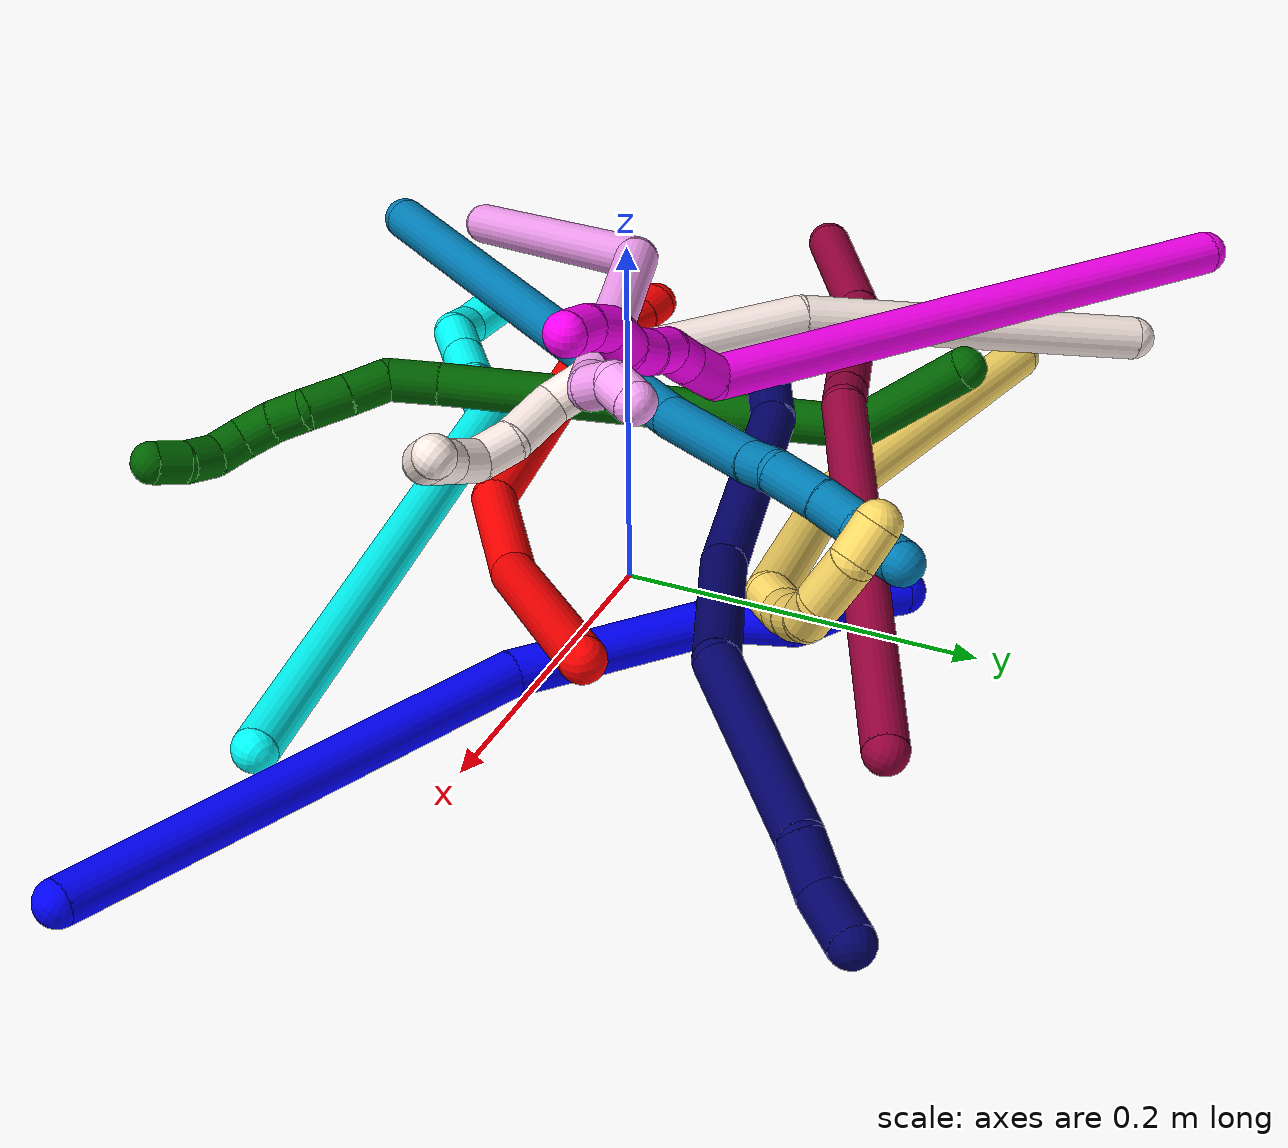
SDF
<sdf version="1.7">
 <world name="default">
  <plugin name="TubeGeneratorPlugin" filename="libtube_generator_plugin.so"/>
  <model name="photoneo_s_sensor">
   <static>1</static>
   <pose>0 0 2 1.57079 1.57079 3.14159</pose>
   <link name="link">
    <inertial><mass>0.1</mass></inertial>
    <sensor name="sensor" type="depth">
     <update_rate>30</update_rate>
     <camera>
      <horizontal_fov>1.22</horizontal_fov>
      <image><width>1920</width><height>1200</height><format>B8G8R8</format></image>
      <clip><near>0.1</near><far>4</far></clip>
      <depth_camera><output>points</output></depth_camera>
     </camera>
     <plugin name="camera_plugin" filename="libgazebo_ros_depth_camera.so">
      <baseline>0.2</baseline>
      <alwaysOn>1</alwaysOn>
      <updateRate>0.0</updateRate>
      <cameraName>camera_ir</cameraName>
      <imageTopicName>/camera/color/image_raw</imageTopicName>
      <cameraInfoTopicName>/camera/color/camera_info</cameraInfoTopicName>
      <depthImageTopicName>/camera/depth/image_raw</depthImageTopicName>
      <depthImageCameraInfoTopicName>/camera/depth/camera_info</depthImageCameraInfoTopicName>
      <pointCloudTopicName>/camera/depth/points</pointCloudTopicName>
      <frameName>fr_optical</frameName>
      <pointCloudCutoff>0.1</pointCloudCutoff>
      <pointCloudCutoffMax>2.0</pointCloudCutoffMax>
      <distortionK1>0</distortionK1>
      <distortionK2>0</distortionK2>
      <distortionK3>0</distortionK3>
      <distortionT1>0</distortionT1>
      <distortionT2>0</distortionT2>
      <CxPrime>0</CxPrime>
      <Cx>0</Cx>
      <Cy>0</Cy>
      <focalLength>0</focalLength>
      <hackBaseline>0</hackBaseline>
     </plugin>
    </sensor>
   </link>
  </model>
  <gravity>0 0 -9.8</gravity>
  <magnetic_field>6e-06 2.3e-05 -4.2e-05</magnetic_field>
  <atmosphere type="adiabatic"/>
  <physics name="default_physics" default="0" type="ode">
   <max_step_size>0.003</max_step_size>
   <real_time_factor>1</real_time_factor>
   <real_time_update_rate>1000</real_time_update_rate>
   <max_contacts>10000</max_contacts>
   <ode>
    <solver>
     <type>quick</type>
     <iters>100</iters>
     <sor>1.3</sor>
     <use_dynamic_moi_rescaling>0</use_dynamic_moi_rescaling>
    </solver>
    <constraints>
     <contact_max_correcting_vel>0</contact_max_correcting_vel>
     <contact_surface_layer>0.001</contact_surface_layer>
     <cfm>0</cfm>
     <erp>0.2</erp>
    </constraints>
   </ode>
  </physics>
  <scene><ambient>0.4 0.4 0.4 1</ambient><background>0.7 0.7 0.7 1</background><shadows>0</shadows></scene>
  <audio><device>default</device></audio>
  <spherical_coordinates>
   <surface_model>EARTH_WGS84</surface_model>
   <latitude_deg>0</latitude_deg>
   <longitude_deg>0</longitude_deg>
   <elevation>0</elevation>
   <heading_deg>0</heading_deg>
  </spherical_coordinates>
  <model name="bin">
   <static>1</static>
   <link name="bottom">
    <collision name="collision-bottom">
     <pose>0 0 -0.01 0 -0 0</pose>
     <geometry><box><size>0.8 0.6 0.02</size></box></geometry>
     <surface>
      <friction><ode><mu>100</mu><mu2>100</mu2></ode></friction>
      <contact><collide_bitmask>65535</collide_bitmask></contact>
     </surface>
    </collision>
   </link>
   <link name="west_wall">
    <collision name="collision-west_wall">
     <pose>-0.41 0 0.1 0 -0 0</pose>
     <geometry><box><size>0.02 0.6 0.2</size></box></geometry>
     <surface>
      <friction><ode><mu>100</mu><mu2>100</mu2></ode></friction>
      <contact><collide_bitmask>65535</collide_bitmask></contact>
     </surface>
    </collision>
   </link>
   <link name="east_wall">
    <collision name="collision-east_wall">
     <pose>0.41 0 0.1 0 -0 0</pose>
     <geometry><box><size>0.02 0.6 0.2</size></box></geometry>
     <surface>
      <friction><ode><mu>100</mu><mu2>100</mu2></ode></friction>
      <contact><collide_bitmask>65535</collide_bitmask></contact>
     </surface>
    </collision>
   </link>
   <link name="south_wall">
    <collision name="collision-south_wall">
     <pose>0 -0.31 0.1 0 -0 0</pose>
     <geometry><box><size>0.8 0.02 0.2</size></box></geometry>
     <surface>
      <friction><ode><mu>100</mu><mu2>100</mu2></ode></friction>
      <contact><collide_bitmask>65535</collide_bitmask></contact>
     </surface>
    </collision>
   </link>
   <link name="north_wall">
    <collision name="collision-north_wall">
     <pose>0 0.31 0.1 0 -0 0</pose>
     <geometry><box><size>0.8 0.02 0.2</size></box></geometry>
     <surface>
      <friction><ode><mu>100</mu><mu2>100</mu2></ode></friction>
      <contact><collide_bitmask>65535</collide_bitmask></contact>
     </surface>
    </collision>
   </link>
  </model>
  <model name="1">
   <static>0</static>
   <link name="1">
    <collision name="collision-cylinder-e_1_1_4">
     <pose>-0.116597 0.062584 -0.035989 -2.09267 -1.01639 1.53292</pose>
     <geometry><cylinder><radius>0.0125</radius><length>0.274276</length></cylinder></geometry>
     <surface>
      <friction><ode><mu>1.16</mu><mu2>1.16</mu2><slip1>0</slip1><slip2>0</slip2></ode></friction>
      <contact><ode><kp>1e+06</kp><kd>1</kd><max_vel>0</max_vel><min_depth>0.001</min_depth></ode></contact>
     </surface>
    </collision>
    <visual name="visual-cylinder-e_1_1_4">
     <pose>-0.116597 0.062584 -0.035989 -2.09267 -1.01639 1.53292</pose>
     <geometry><cylinder><radius>0.0125</radius><length>0.274276</length></cylinder></geometry>
     <material><ambient>0 0 1 1</ambient></material>
    </visual>
    <collision name="collision-cylinder-e_2_4_5">
     <pose>-0.281978 0.135313 -0.091669 -2.66589 -1.14458 2.4217</pose>
     <geometry><cylinder><radius>0.0125</radius><length>0.107154</length></cylinder></geometry>
     <surface>
      <friction><ode><mu>1.16</mu><mu2>1.16</mu2><slip1>0</slip1><slip2>0</slip2></ode></friction>
      <contact><ode><kp>1e+06</kp><kd>1</kd><max_vel>0</max_vel><min_depth>0.001</min_depth></ode></contact>
     </surface>
    </collision>
    <visual name="visual-cylinder-e_2_4_5">
     <pose>-0.281978 0.135313 -0.091669 -2.66589 -1.14458 2.4217</pose>
     <geometry><cylinder><radius>0.0125</radius><length>0.107154</length></cylinder></geometry>
     <material><ambient>0 0 1 1</ambient></material>
    </visual>
    <collision name="collision-cylinder-e_3_5_6">
     <pose>-0.339688 0.145139 -0.116277 3.07688 -1.06649 -3.03204</pose>
     <geometry><cylinder><radius>0.0125</radius><length>0.020391</length></cylinder></geometry>
     <surface>
      <friction><ode><mu>1.16</mu><mu2>1.16</mu2><slip1>0</slip1><slip2>0</slip2></ode></friction>
      <contact><ode><kp>1e+06</kp><kd>1</kd><max_vel>0</max_vel><min_depth>0.001</min_depth></ode></contact>
     </surface>
    </collision>
    <visual name="visual-cylinder-e_3_5_6">
     <pose>-0.339688 0.145139 -0.116277 3.07688 -1.06649 -3.03204</pose>
     <geometry><cylinder><radius>0.0125</radius><length>0.020391</length></cylinder></geometry>
     <material><ambient>0 0 1 1</ambient></material>
    </visual>
    <collision name="collision-cylinder-e_4_6_7">
     <pose>-0.36118 0.139467 -0.129032 2.54247 -0.923789 -2.03098</pose>
     <geometry><cylinder><radius>0.0125</radius><length>0.031495</length></cylinder></geometry>
     <surface>
      <friction><ode><mu>1.16</mu><mu2>1.16</mu2><slip1>0</slip1><slip2>0</slip2></ode></friction>
      <contact><ode><kp>1e+06</kp><kd>1</kd><max_vel>0</max_vel><min_depth>0.001</min_depth></ode></contact>
     </surface>
    </collision>
    <visual name="visual-cylinder-e_4_6_7">
     <pose>-0.36118 0.139467 -0.129032 2.54247 -0.923789 -2.03098</pose>
     <geometry><cylinder><radius>0.0125</radius><length>0.031495</length></cylinder></geometry>
     <material><ambient>0 0 1 1</ambient></material>
    </visual>
    <collision name="collision-cylinder-e_5_7_8">
     <pose>-0.384255 0.137928 -0.141032 -2.39957 -1.07799 1.98818</pose>
     <geometry><cylinder><radius>0.0125</radius><length>0.023859</length></cylinder></geometry>
     <surface>
      <friction><ode><mu>1.16</mu><mu2>1.16</mu2><slip1>0</slip1><slip2>0</slip2></ode></friction>
      <contact><ode><kp>1e+06</kp><kd>1</kd><max_vel>0</max_vel><min_depth>0.001</min_depth></ode></contact>
     </surface>
    </collision>
    <visual name="visual-cylinder-e_5_7_8">
     <pose>-0.384255 0.137928 -0.141032 -2.39957 -1.07799 1.98818</pose>
     <geometry><cylinder><radius>0.0125</radius><length>0.023859</length></cylinder></geometry>
     <material><ambient>0 0 1 1</ambient></material>
    </visual>
    <collision name="collision-cylinder-e_6_8_9">
     <pose>-0.404079 0.144809 -0.149055 -2.47045 -1.0838 2.09144</pose>
     <geometry><cylinder><radius>0.0125</radius><length>0.021079</length></cylinder></geometry>
     <surface>
      <friction><ode><mu>1.16</mu><mu2>1.16</mu2><slip1>0</slip1><slip2>0</slip2></ode></friction>
      <contact><ode><kp>1e+06</kp><kd>1</kd><max_vel>0</max_vel><min_depth>0.001</min_depth></ode></contact>
     </surface>
    </collision>
    <visual name="visual-cylinder-e_6_8_9">
     <pose>-0.404079 0.144809 -0.149055 -2.47045 -1.0838 2.09144</pose>
     <geometry><cylinder><radius>0.0125</radius><length>0.021079</length></cylinder></geometry>
     <material><ambient>0 0 1 1</ambient></material>
    </visual>
    <collision name="collision-cylinder-e_7_9_2">
     <pose>-0.423621 0.148818 -0.156482 -2.88331 -1.22473 2.77597</pose>
     <geometry><cylinder><radius>0.0125</radius><length>0.021744</length></cylinder></geometry>
     <surface>
      <friction><ode><mu>1.16</mu><mu2>1.16</mu2><slip1>0</slip1><slip2>0</slip2></ode></friction>
      <contact><ode><kp>1e+06</kp><kd>1</kd><max_vel>0</max_vel><min_depth>0.001</min_depth></ode></contact>
     </surface>
    </collision>
    <visual name="visual-cylinder-e_7_9_2">
     <pose>-0.423621 0.148818 -0.156482 -2.88331 -1.22473 2.77597</pose>
     <geometry><cylinder><radius>0.0125</radius><length>0.021744</length></cylinder></geometry>
     <material><ambient>0 0 1 1</ambient></material>
    </visual>
    <collision name="collision-sphere-2">
     <pose>-0.433848 0.14976 -0.160048 0 -0 0</pose>
     <geometry><sphere><radius>0.0125</radius></sphere></geometry>
     <surface>
      <friction><ode><mu>1.16</mu><mu2>1.16</mu2><slip1>0</slip1><slip2>0</slip2></ode></friction>
      <contact><ode><kp>1e+06</kp><kd>1</kd><max_vel>0</max_vel><min_depth>0.001</min_depth></ode></contact>
     </surface>
    </collision>
    <visual name="visual-sphere-2">
     <pose>-0.433848 0.14976 -0.160048 0 -0 0</pose>
     <geometry><sphere><radius>0.0125</radius></sphere></geometry>
     <material><ambient>0 0 1 1</ambient></material>
    </visual>
    <collision name="collision-sphere-9">
     <pose>-0.413394 0.147876 -0.152917 0 -0 0</pose>
     <geometry><sphere><radius>0.0125</radius></sphere></geometry>
     <surface>
      <friction><ode><mu>1.16</mu><mu2>1.16</mu2><slip1>0</slip1><slip2>0</slip2></ode></friction>
      <contact><ode><kp>1e+06</kp><kd>1</kd><max_vel>0</max_vel><min_depth>0.001</min_depth></ode></contact>
     </surface>
    </collision>
    <visual name="visual-sphere-9">
     <pose>-0.413394 0.147876 -0.152917 0 -0 0</pose>
     <geometry><sphere><radius>0.0125</radius></sphere></geometry>
     <material><ambient>0 0 1 1</ambient></material>
    </visual>
    <collision name="collision-sphere-4">
     <pose>-0.233194 0.125169 -0.071978 0 -0 0</pose>
     <geometry><sphere><radius>0.0125</radius></sphere></geometry>
     <surface>
      <friction><ode><mu>1.16</mu><mu2>1.16</mu2><slip1>0</slip1><slip2>0</slip2></ode></friction>
      <contact><ode><kp>1e+06</kp><kd>1</kd><max_vel>0</max_vel><min_depth>0.001</min_depth></ode></contact>
     </surface>
    </collision>
    <visual name="visual-sphere-4">
     <pose>-0.233194 0.125169 -0.071978 0 -0 0</pose>
     <geometry><sphere><radius>0.0125</radius></sphere></geometry>
     <material><ambient>0 0 1 1</ambient></material>
    </visual>
    <collision name="collision-sphere-1">
     <geometry><sphere><radius>0.0125</radius></sphere></geometry>
     <surface>
      <friction><ode><mu>1.16</mu><mu2>1.16</mu2><slip1>0</slip1><slip2>0</slip2></ode></friction>
      <contact><ode><kp>1e+06</kp><kd>1</kd><max_vel>0</max_vel><min_depth>0.001</min_depth></ode></contact>
     </surface>
    </collision>
    <visual name="visual-sphere-1">
     <geometry><sphere><radius>0.0125</radius></sphere></geometry>
     <material><ambient>0 0 1 1</ambient></material>
    </visual>
    <collision name="collision-sphere-8">
     <pose>-0.394765 0.141742 -0.145192 0 -0 0</pose>
     <geometry><sphere><radius>0.0125</radius></sphere></geometry>
     <surface>
      <friction><ode><mu>1.16</mu><mu2>1.16</mu2><slip1>0</slip1><slip2>0</slip2></ode></friction>
      <contact><ode><kp>1e+06</kp><kd>1</kd><max_vel>0</max_vel><min_depth>0.001</min_depth></ode></contact>
     </surface>
    </collision>
    <visual name="visual-sphere-8">
     <pose>-0.394765 0.141742 -0.145192 0 -0 0</pose>
     <geometry><sphere><radius>0.0125</radius></sphere></geometry>
     <material><ambient>0 0 1 1</ambient></material>
    </visual>
    <collision name="collision-sphere-5">
     <pose>-0.330762 0.145457 -0.11136 0 -0 0</pose>
     <geometry><sphere><radius>0.0125</radius></sphere></geometry>
     <surface>
      <friction><ode><mu>1.16</mu><mu2>1.16</mu2><slip1>0</slip1><slip2>0</slip2></ode></friction>
      <contact><ode><kp>1e+06</kp><kd>1</kd><max_vel>0</max_vel><min_depth>0.001</min_depth></ode></contact>
     </surface>
    </collision>
    <visual name="visual-sphere-5">
     <pose>-0.330762 0.145457 -0.11136 0 -0 0</pose>
     <geometry><sphere><radius>0.0125</radius></sphere></geometry>
     <material><ambient>0 0 1 1</ambient></material>
    </visual>
    <collision name="collision-sphere-6">
     <pose>-0.348615 0.14482 -0.121193 0 -0 0</pose>
     <geometry><sphere><radius>0.0125</radius></sphere></geometry>
     <surface>
      <friction><ode><mu>1.16</mu><mu2>1.16</mu2><slip1>0</slip1><slip2>0</slip2></ode></friction>
      <contact><ode><kp>1e+06</kp><kd>1</kd><max_vel>0</max_vel><min_depth>0.001</min_depth></ode></contact>
     </surface>
    </collision>
    <visual name="visual-sphere-6">
     <pose>-0.348615 0.14482 -0.121193 0 -0 0</pose>
     <geometry><sphere><radius>0.0125</radius></sphere></geometry>
     <material><ambient>0 0 1 1</ambient></material>
    </visual>
    <collision name="collision-sphere-7">
     <pose>-0.373745 0.134114 -0.136872 0 -0 0</pose>
     <geometry><sphere><radius>0.0125</radius></sphere></geometry>
     <surface>
      <friction><ode><mu>1.16</mu><mu2>1.16</mu2><slip1>0</slip1><slip2>0</slip2></ode></friction>
      <contact><ode><kp>1e+06</kp><kd>1</kd><max_vel>0</max_vel><min_depth>0.001</min_depth></ode></contact>
     </surface>
    </collision>
    <visual name="visual-sphere-7">
     <pose>-0.373745 0.134114 -0.136872 0 -0 0</pose>
     <geometry><sphere><radius>0.0125</radius></sphere></geometry>
     <material><ambient>0 0 1 1</ambient></material>
    </visual>
    <inertial>
     <pose>-0.214788 0.097192 -0.072076 0 -0 0</pose>
     <mass>0.5</mass>
     <inertia>
      <ixx>0.000903</ixx>
      <ixy>0</ixy>
      <ixz>0</ixz>
      <iyy>0.002302</iyy>
      <iyz>0</iyz>
      <izz>0.000755</izz>
     </inertia>
    </inertial>
   </link>
   <pose>0.381117 -0.116056 0.011761 2.81207 -0.430287 -0.760575</pose>
  </model>
  <model name="2">
   <static>0</static>
   <link name="2">
    <collision name="collision-cylinder-e_1_1_4">
     <pose>-0.0543 -0.049568 -0.039005 2.23749 -0.710783 -1.30523</pose>
     <geometry><cylinder><radius>0.0125</radius><length>0.166456</length></cylinder></geometry>
     <surface>
      <friction><ode><mu>1.16</mu><mu2>1.16</mu2><slip1>0</slip1><slip2>0</slip2></ode></friction>
      <contact><ode><kp>1e+06</kp><kd>1</kd><max_vel>0</max_vel><min_depth>0.001</min_depth></ode></contact>
     </surface>
    </collision>
    <visual name="visual-cylinder-e_1_1_4">
     <pose>-0.0543 -0.049568 -0.039005 2.23749 -0.710783 -1.30523</pose>
     <geometry><cylinder><radius>0.0125</radius><length>0.166456</length></cylinder></geometry>
     <material><ambient>1 0 0 1</ambient></material>
    </visual>
    <collision name="collision-cylinder-e_2_4_5">
     <pose>-0.141131 -0.120472 -0.087082 1.97285 -0.951593 -1.32365</pose>
     <geometry><cylinder><radius>0.0125</radius><length>0.079894</length></cylinder></geometry>
     <surface>
      <friction><ode><mu>1.16</mu><mu2>1.16</mu2><slip1>0</slip1><slip2>0</slip2></ode></friction>
      <contact><ode><kp>1e+06</kp><kd>1</kd><max_vel>0</max_vel><min_depth>0.001</min_depth></ode></contact>
     </surface>
    </collision>
    <visual name="visual-cylinder-e_2_4_5">
     <pose>-0.141131 -0.120472 -0.087082 1.97285 -0.951593 -1.32365</pose>
     <geometry><cylinder><radius>0.0125</radius><length>0.079894</length></cylinder></geometry>
     <material><ambient>1 0 0 1</ambient></material>
    </visual>
    <collision name="collision-cylinder-e_3_5_6">
     <pose>-0.246547 -0.148079 -0.117651 2.85776 -1.27272 -2.75958</pose>
     <geometry><cylinder><radius>0.0125</radius><length>0.152496</length></cylinder></geometry>
     <surface>
      <friction><ode><mu>1.16</mu><mu2>1.16</mu2><slip1>0</slip1><slip2>0</slip2></ode></friction>
      <contact><ode><kp>1e+06</kp><kd>1</kd><max_vel>0</max_vel><min_depth>0.001</min_depth></ode></contact>
     </surface>
    </collision>
    <visual name="visual-cylinder-e_3_5_6">
     <pose>-0.246547 -0.148079 -0.117651 2.85776 -1.27272 -2.75958</pose>
     <geometry><cylinder><radius>0.0125</radius><length>0.152496</length></cylinder></geometry>
     <material><ambient>1 0 0 1</ambient></material>
    </visual>
    <collision name="collision-cylinder-e_4_6_7">
     <pose>-0.330114 -0.154778 -0.138539 0.613105 -1.50119 -0.574152</pose>
     <geometry><cylinder><radius>0.0125</radius><length>0.021415</length></cylinder></geometry>
     <surface>
      <friction><ode><mu>1.16</mu><mu2>1.16</mu2><slip1>0</slip1><slip2>0</slip2></ode></friction>
      <contact><ode><kp>1e+06</kp><kd>1</kd><max_vel>0</max_vel><min_depth>0.001</min_depth></ode></contact>
     </surface>
    </collision>
    <visual name="visual-cylinder-e_4_6_7">
     <pose>-0.330114 -0.154778 -0.138539 0.613105 -1.50119 -0.574152</pose>
     <geometry><cylinder><radius>0.0125</radius><length>0.021415</length></cylinder></geometry>
     <material><ambient>1 0 0 1</ambient></material>
    </visual>
    <collision name="collision-cylinder-e_5_7_8">
     <pose>-0.357824 -0.153846 -0.14716 -2.99525 -1.06952 2.89534</pose>
     <geometry><cylinder><radius>0.0125</radius><length>0.038833</length></cylinder></geometry>
     <surface>
      <friction><ode><mu>1.16</mu><mu2>1.16</mu2><slip1>0</slip1><slip2>0</slip2></ode></friction>
      <contact><ode><kp>1e+06</kp><kd>1</kd><max_vel>0</max_vel><min_depth>0.001</min_depth></ode></contact>
     </surface>
    </collision>
    <visual name="visual-cylinder-e_5_7_8">
     <pose>-0.357824 -0.153846 -0.14716 -2.99525 -1.06952 2.89534</pose>
     <geometry><cylinder><radius>0.0125</radius><length>0.038833</length></cylinder></geometry>
     <material><ambient>1 0 0 1</ambient></material>
    </visual>
    <collision name="collision-cylinder-e_6_8_9">
     <pose>-0.383787 -0.150336 -0.160911 -2.6978 -1.06026 2.40667</pose>
     <geometry><cylinder><radius>0.0125</radius><length>0.020484</length></cylinder></geometry>
     <surface>
      <friction><ode><mu>1.16</mu><mu2>1.16</mu2><slip1>0</slip1><slip2>0</slip2></ode></friction>
      <contact><ode><kp>1e+06</kp><kd>1</kd><max_vel>0</max_vel><min_depth>0.001</min_depth></ode></contact>
     </surface>
    </collision>
    <visual name="visual-cylinder-e_6_8_9">
     <pose>-0.383787 -0.150336 -0.160911 -2.6978 -1.06026 2.40667</pose>
     <geometry><cylinder><radius>0.0125</radius><length>0.020484</length></cylinder></geometry>
     <material><ambient>1 0 0 1</ambient></material>
    </visual>
    <collision name="collision-cylinder-e_7_9_2">
     <pose>-0.40224 -0.146812 -0.168866 -2.76076 -1.20002 2.59235</pose>
     <geometry><cylinder><radius>0.0125</radius><length>0.020422</length></cylinder></geometry>
     <surface>
      <friction><ode><mu>1.16</mu><mu2>1.16</mu2><slip1>0</slip1><slip2>0</slip2></ode></friction>
      <contact><ode><kp>1e+06</kp><kd>1</kd><max_vel>0</max_vel><min_depth>0.001</min_depth></ode></contact>
     </surface>
    </collision>
    <visual name="visual-cylinder-e_7_9_2">
     <pose>-0.40224 -0.146812 -0.168866 -2.76076 -1.20002 2.59235</pose>
     <geometry><cylinder><radius>0.0125</radius><length>0.020422</length></cylinder></geometry>
     <material><ambient>1 0 0 1</ambient></material>
    </visual>
    <collision name="collision-sphere-2">
     <pose>-0.411758 -0.145437 -0.172301 0 -0 0</pose>
     <geometry><sphere><radius>0.0125</radius></sphere></geometry>
     <surface>
      <friction><ode><mu>1.16</mu><mu2>1.16</mu2><slip1>0</slip1><slip2>0</slip2></ode></friction>
      <contact><ode><kp>1e+06</kp><kd>1</kd><max_vel>0</max_vel><min_depth>0.001</min_depth></ode></contact>
     </surface>
    </collision>
    <visual name="visual-sphere-2">
     <pose>-0.411758 -0.145437 -0.172301 0 -0 0</pose>
     <geometry><sphere><radius>0.0125</radius></sphere></geometry>
     <material><ambient>1 0 0 1</ambient></material>
    </visual>
    <collision name="collision-sphere-9">
     <pose>-0.392723 -0.148188 -0.165431 0 -0 0</pose>
     <geometry><sphere><radius>0.0125</radius></sphere></geometry>
     <surface>
      <friction><ode><mu>1.16</mu><mu2>1.16</mu2><slip1>0</slip1><slip2>0</slip2></ode></friction>
      <contact><ode><kp>1e+06</kp><kd>1</kd><max_vel>0</max_vel><min_depth>0.001</min_depth></ode></contact>
     </surface>
    </collision>
    <visual name="visual-sphere-9">
     <pose>-0.392723 -0.148188 -0.165431 0 -0 0</pose>
     <geometry><sphere><radius>0.0125</radius></sphere></geometry>
     <material><ambient>1 0 0 1</ambient></material>
    </visual>
    <collision name="collision-sphere-4">
     <pose>-0.1086 -0.099136 -0.07801 0 -0 0</pose>
     <geometry><sphere><radius>0.0125</radius></sphere></geometry>
     <surface>
      <friction><ode><mu>1.16</mu><mu2>1.16</mu2><slip1>0</slip1><slip2>0</slip2></ode></friction>
      <contact><ode><kp>1e+06</kp><kd>1</kd><max_vel>0</max_vel><min_depth>0.001</min_depth></ode></contact>
     </surface>
    </collision>
    <visual name="visual-sphere-4">
     <pose>-0.1086 -0.099136 -0.07801 0 -0 0</pose>
     <geometry><sphere><radius>0.0125</radius></sphere></geometry>
     <material><ambient>1 0 0 1</ambient></material>
    </visual>
    <collision name="collision-sphere-1">
     <geometry><sphere><radius>0.0125</radius></sphere></geometry>
     <surface>
      <friction><ode><mu>1.16</mu><mu2>1.16</mu2><slip1>0</slip1><slip2>0</slip2></ode></friction>
      <contact><ode><kp>1e+06</kp><kd>1</kd><max_vel>0</max_vel><min_depth>0.001</min_depth></ode></contact>
     </surface>
    </collision>
    <visual name="visual-sphere-1">
     <geometry><sphere><radius>0.0125</radius></sphere></geometry>
     <material><ambient>1 0 0 1</ambient></material>
    </visual>
    <collision name="collision-sphere-8">
     <pose>-0.374851 -0.152485 -0.156391 0 -0 0</pose>
     <geometry><sphere><radius>0.0125</radius></sphere></geometry>
     <surface>
      <friction><ode><mu>1.16</mu><mu2>1.16</mu2><slip1>0</slip1><slip2>0</slip2></ode></friction>
      <contact><ode><kp>1e+06</kp><kd>1</kd><max_vel>0</max_vel><min_depth>0.001</min_depth></ode></contact>
     </surface>
    </collision>
    <visual name="visual-sphere-8">
     <pose>-0.374851 -0.152485 -0.156391 0 -0 0</pose>
     <geometry><sphere><radius>0.0125</radius></sphere></geometry>
     <material><ambient>1 0 0 1</ambient></material>
    </visual>
    <collision name="collision-sphere-5">
     <pose>-0.173661 -0.141808 -0.096154 0 -0 0</pose>
     <geometry><sphere><radius>0.0125</radius></sphere></geometry>
     <surface>
      <friction><ode><mu>1.16</mu><mu2>1.16</mu2><slip1>0</slip1><slip2>0</slip2></ode></friction>
      <contact><ode><kp>1e+06</kp><kd>1</kd><max_vel>0</max_vel><min_depth>0.001</min_depth></ode></contact>
     </surface>
    </collision>
    <visual name="visual-sphere-5">
     <pose>-0.173661 -0.141808 -0.096154 0 -0 0</pose>
     <geometry><sphere><radius>0.0125</radius></sphere></geometry>
     <material><ambient>1 0 0 1</ambient></material>
    </visual>
    <collision name="collision-sphere-6">
     <pose>-0.319433 -0.154349 -0.139148 0 -0 0</pose>
     <geometry><sphere><radius>0.0125</radius></sphere></geometry>
     <surface>
      <friction><ode><mu>1.16</mu><mu2>1.16</mu2><slip1>0</slip1><slip2>0</slip2></ode></friction>
      <contact><ode><kp>1e+06</kp><kd>1</kd><max_vel>0</max_vel><min_depth>0.001</min_depth></ode></contact>
     </surface>
    </collision>
    <visual name="visual-sphere-6">
     <pose>-0.319433 -0.154349 -0.139148 0 -0 0</pose>
     <geometry><sphere><radius>0.0125</radius></sphere></geometry>
     <material><ambient>1 0 0 1</ambient></material>
    </visual>
    <collision name="collision-sphere-7">
     <pose>-0.340796 -0.155206 -0.13793 0 -0 0</pose>
     <geometry><sphere><radius>0.0125</radius></sphere></geometry>
     <surface>
      <friction><ode><mu>1.16</mu><mu2>1.16</mu2><slip1>0</slip1><slip2>0</slip2></ode></friction>
      <contact><ode><kp>1e+06</kp><kd>1</kd><max_vel>0</max_vel><min_depth>0.001</min_depth></ode></contact>
     </surface>
    </collision>
    <visual name="visual-sphere-7">
     <pose>-0.340796 -0.155206 -0.13793 0 -0 0</pose>
     <geometry><sphere><radius>0.0125</radius></sphere></geometry>
     <material><ambient>1 0 0 1</ambient></material>
    </visual>
    <inertial>
     <pose>-0.189905 -0.111648 -0.093635 0 -0 0</pose>
     <mass>0.5</mass>
     <inertia>
      <ixx>-0.000377</ixx>
      <ixy>0</ixy>
      <ixz>0</ixz>
      <iyy>0.000114</iyy>
      <iyz>0</iyz>
      <izz>0.000858</izz>
     </inertia>
    </inertial>
   </link>
   <pose>0.163731 0.050842 0.059449 0.073109 0.311316 0.06362</pose>
  </model>
  <model name="3">
   <static>0</static>
   <link name="3">
    <collision name="collision-cylinder-e_1_1_4">
     <pose>-0.144507 -0.022267 0.096049 0.227804 -0.972054 -0.120724</pose>
     <geometry><cylinder><radius>0.0125</radius><length>0.349877</length></cylinder></geometry>
     <surface>
      <friction><ode><mu>1.16</mu><mu2>1.16</mu2><slip1>0</slip1><slip2>0</slip2></ode></friction>
      <contact><ode><kp>1e+06</kp><kd>1</kd><max_vel>0</max_vel><min_depth>0.001</min_depth></ode></contact>
     </surface>
    </collision>
    <visual name="visual-cylinder-e_1_1_4">
     <pose>-0.144507 -0.022267 0.096049 0.227804 -0.972054 -0.120724</pose>
     <geometry><cylinder><radius>0.0125</radius><length>0.349877</length></cylinder></geometry>
     <material><ambient>0.003922 1 0.996078 1</ambient></material>
    </visual>
    <collision name="collision-cylinder-e_2_4_5">
     <pose>-0.294638 -0.04295 0.206939 -0.106335 -0.360307 0.019384</pose>
     <geometry><cylinder><radius>0.0125</radius><length>0.0319</length></cylinder></geometry>
     <surface>
      <friction><ode><mu>1.16</mu><mu2>1.16</mu2><slip1>0</slip1><slip2>0</slip2></ode></friction>
      <contact><ode><kp>1e+06</kp><kd>1</kd><max_vel>0</max_vel><min_depth>0.001</min_depth></ode></contact>
     </surface>
    </collision>
    <visual name="visual-cylinder-e_2_4_5">
     <pose>-0.294638 -0.04295 0.206939 -0.106335 -0.360307 0.019384</pose>
     <geometry><cylinder><radius>0.0125</radius><length>0.0319</length></cylinder></geometry>
     <material><ambient>0.003922 1 0.996078 1</ambient></material>
    </visual>
    <collision name="collision-cylinder-e_3_5_6">
     <pose>-0.307636 -0.043592 0.236748 0.147694 -0.4535 -0.034134</pose>
     <geometry><cylinder><radius>0.0125</radius><length>0.033666</length></cylinder></geometry>
     <surface>
      <friction><ode><mu>1.16</mu><mu2>1.16</mu2><slip1>0</slip1><slip2>0</slip2></ode></friction>
      <contact><ode><kp>1e+06</kp><kd>1</kd><max_vel>0</max_vel><min_depth>0.001</min_depth></ode></contact>
     </surface>
    </collision>
    <visual name="visual-cylinder-e_3_5_6">
     <pose>-0.307636 -0.043592 0.236748 0.147694 -0.4535 -0.034134</pose>
     <geometry><cylinder><radius>0.0125</radius><length>0.033666</length></cylinder></geometry>
     <material><ambient>0.003922 1 0.996078 1</ambient></material>
    </visual>
    <collision name="collision-cylinder-e_4_6_7">
     <pose>-0.321472 -0.04668 0.26499 0.064788 -0.452185 -0.014908</pose>
     <geometry><cylinder><radius>0.0125</radius><length>0.02958</length></cylinder></geometry>
     <surface>
      <friction><ode><mu>1.16</mu><mu2>1.16</mu2><slip1>0</slip1><slip2>0</slip2></ode></friction>
      <contact><ode><kp>1e+06</kp><kd>1</kd><max_vel>0</max_vel><min_depth>0.001</min_depth></ode></contact>
     </surface>
    </collision>
    <visual name="visual-cylinder-e_4_6_7">
     <pose>-0.321472 -0.04668 0.26499 0.064788 -0.452185 -0.014908</pose>
     <geometry><cylinder><radius>0.0125</radius><length>0.02958</length></cylinder></geometry>
     <material><ambient>0.003922 1 0.996078 1</ambient></material>
    </visual>
    <collision name="collision-cylinder-e_5_7_8">
     <pose>-0.336401 -0.051808 0.283205 0.712399 -0.914018 -0.361913</pose>
     <geometry><cylinder><radius>0.0125</radius><length>0.02138</length></cylinder></geometry>
     <surface>
      <friction><ode><mu>1.16</mu><mu2>1.16</mu2><slip1>0</slip1><slip2>0</slip2></ode></friction>
      <contact><ode><kp>1e+06</kp><kd>1</kd><max_vel>0</max_vel><min_depth>0.001</min_depth></ode></contact>
     </surface>
    </collision>
    <visual name="visual-cylinder-e_5_7_8">
     <pose>-0.336401 -0.051808 0.283205 0.712399 -0.914018 -0.361913</pose>
     <geometry><cylinder><radius>0.0125</radius><length>0.02138</length></cylinder></geometry>
     <material><ambient>0.003922 1 0.996078 1</ambient></material>
    </visual>
    <collision name="collision-cylinder-e_6_8_2">
     <pose>-0.361409 -0.055863 0.291062 -0.072186 -1.39575 0.060547</pose>
     <geometry><cylinder><radius>0.0125</radius><length>0.033598</length></cylinder></geometry>
     <surface>
      <friction><ode><mu>1.16</mu><mu2>1.16</mu2><slip1>0</slip1><slip2>0</slip2></ode></friction>
      <contact><ode><kp>1e+06</kp><kd>1</kd><max_vel>0</max_vel><min_depth>0.001</min_depth></ode></contact>
     </surface>
    </collision>
    <visual name="visual-cylinder-e_6_8_2">
     <pose>-0.361409 -0.055863 0.291062 -0.072186 -1.39575 0.060547</pose>
     <geometry><cylinder><radius>0.0125</radius><length>0.033598</length></cylinder></geometry>
     <material><ambient>0.003922 1 0.996078 1</ambient></material>
    </visual>
    <collision name="collision-sphere-2">
     <pose>-0.377951 -0.055652 0.29398 0 -0 0</pose>
     <geometry><sphere><radius>0.0125</radius></sphere></geometry>
     <surface>
      <friction><ode><mu>1.16</mu><mu2>1.16</mu2><slip1>0</slip1><slip2>0</slip2></ode></friction>
      <contact><ode><kp>1e+06</kp><kd>1</kd><max_vel>0</max_vel><min_depth>0.001</min_depth></ode></contact>
     </surface>
    </collision>
    <visual name="visual-sphere-2">
     <pose>-0.377951 -0.055652 0.29398 0 -0 0</pose>
     <geometry><sphere><radius>0.0125</radius></sphere></geometry>
     <material><ambient>0.003922 1 0.996078 1</ambient></material>
    </visual>
    <collision name="collision-sphere-4">
     <pose>-0.289014 -0.044534 0.192098 0 -0 0</pose>
     <geometry><sphere><radius>0.0125</radius></sphere></geometry>
     <surface>
      <friction><ode><mu>1.16</mu><mu2>1.16</mu2><slip1>0</slip1><slip2>0</slip2></ode></friction>
      <contact><ode><kp>1e+06</kp><kd>1</kd><max_vel>0</max_vel><min_depth>0.001</min_depth></ode></contact>
     </surface>
    </collision>
    <visual name="visual-sphere-4">
     <pose>-0.289014 -0.044534 0.192098 0 -0 0</pose>
     <geometry><sphere><radius>0.0125</radius></sphere></geometry>
     <material><ambient>0.003922 1 0.996078 1</ambient></material>
    </visual>
    <collision name="collision-sphere-1">
     <geometry><sphere><radius>0.0125</radius></sphere></geometry>
     <surface>
      <friction><ode><mu>1.16</mu><mu2>1.16</mu2><slip1>0</slip1><slip2>0</slip2></ode></friction>
      <contact><ode><kp>1e+06</kp><kd>1</kd><max_vel>0</max_vel><min_depth>0.001</min_depth></ode></contact>
     </surface>
    </collision>
    <visual name="visual-sphere-1">
     <geometry><sphere><radius>0.0125</radius></sphere></geometry>
     <material><ambient>0.003922 1 0.996078 1</ambient></material>
    </visual>
    <collision name="collision-sphere-8">
     <pose>-0.344867 -0.056074 0.288144 0 -0 0</pose>
     <geometry><sphere><radius>0.0125</radius></sphere></geometry>
     <surface>
      <friction><ode><mu>1.16</mu><mu2>1.16</mu2><slip1>0</slip1><slip2>0</slip2></ode></friction>
      <contact><ode><kp>1e+06</kp><kd>1</kd><max_vel>0</max_vel><min_depth>0.001</min_depth></ode></contact>
     </surface>
    </collision>
    <visual name="visual-sphere-8">
     <pose>-0.344867 -0.056074 0.288144 0 -0 0</pose>
     <geometry><sphere><radius>0.0125</radius></sphere></geometry>
     <material><ambient>0.003922 1 0.996078 1</ambient></material>
    </visual>
    <collision name="collision-sphere-5">
     <pose>-0.300261 -0.041365 0.221781 0 -0 0</pose>
     <geometry><sphere><radius>0.0125</radius></sphere></geometry>
     <surface>
      <friction><ode><mu>1.16</mu><mu2>1.16</mu2><slip1>0</slip1><slip2>0</slip2></ode></friction>
      <contact><ode><kp>1e+06</kp><kd>1</kd><max_vel>0</max_vel><min_depth>0.001</min_depth></ode></contact>
     </surface>
    </collision>
    <visual name="visual-sphere-5">
     <pose>-0.300261 -0.041365 0.221781 0 -0 0</pose>
     <geometry><sphere><radius>0.0125</radius></sphere></geometry>
     <material><ambient>0.003922 1 0.996078 1</ambient></material>
    </visual>
    <collision name="collision-sphere-6">
     <pose>-0.31501 -0.045819 0.251714 0 -0 0</pose>
     <geometry><sphere><radius>0.0125</radius></sphere></geometry>
     <surface>
      <friction><ode><mu>1.16</mu><mu2>1.16</mu2><slip1>0</slip1><slip2>0</slip2></ode></friction>
      <contact><ode><kp>1e+06</kp><kd>1</kd><max_vel>0</max_vel><min_depth>0.001</min_depth></ode></contact>
     </surface>
    </collision>
    <visual name="visual-sphere-6">
     <pose>-0.31501 -0.045819 0.251714 0 -0 0</pose>
     <geometry><sphere><radius>0.0125</radius></sphere></geometry>
     <material><ambient>0.003922 1 0.996078 1</ambient></material>
    </visual>
    <collision name="collision-sphere-7">
     <pose>-0.327935 -0.047541 0.278265 0 -0 0</pose>
     <geometry><sphere><radius>0.0125</radius></sphere></geometry>
     <surface>
      <friction><ode><mu>1.16</mu><mu2>1.16</mu2><slip1>0</slip1><slip2>0</slip2></ode></friction>
      <contact><ode><kp>1e+06</kp><kd>1</kd><max_vel>0</max_vel><min_depth>0.001</min_depth></ode></contact>
     </surface>
    </collision>
    <visual name="visual-sphere-7">
     <pose>-0.327935 -0.047541 0.278265 0 -0 0</pose>
     <geometry><sphere><radius>0.0125</radius></sphere></geometry>
     <material><ambient>0.003922 1 0.996078 1</ambient></material>
    </visual>
    <inertial>
     <pose>-0.198318 -0.029987 0.143698 0 -0 0</pose>
     <mass>0.5</mass>
     <inertia>
      <ixx>0.001744</ixx>
      <ixy>0</ixy>
      <ixz>0</ixz>
      <iyy>0.003315</iyy>
      <iyz>0</iyz>
      <izz>0.00345</izz>
     </inertia>
    </inertial>
   </link>
   <pose>0.238249 -0.094344 0.012269 1.52432 0.120449 -0.454143</pose>
  </model>
  <model name="4">
   <static>0</static>
   <link name="4">
    <collision name="collision-cylinder-e_1_1_4">
     <pose>-0.004782 -0.009006 -0.128204 3.07146 -0.03719 -0.974888</pose>
     <geometry><cylinder><radius>0.0125</radius><length>0.257218</length></cylinder></geometry>
     <surface>
      <friction><ode><mu>1.16</mu><mu2>1.16</mu2><slip1>0</slip1><slip2>0</slip2></ode></friction>
      <contact><ode><kp>1e+06</kp><kd>1</kd><max_vel>0</max_vel><min_depth>0.001</min_depth></ode></contact>
     </surface>
    </collision>
    <visual name="visual-cylinder-e_1_1_4">
     <pose>-0.004782 -0.009006 -0.128204 3.07146 -0.03719 -0.974888</pose>
     <geometry><cylinder><radius>0.0125</radius><length>0.257218</length></cylinder></geometry>
     <material><ambient>1 0.65098 0.996078 1</ambient></material>
    </visual>
    <collision name="collision-cylinder-e_2_4_5">
     <pose>-0.051735 0.0076 -0.330928 -2.81054 -0.491392 1.96626</pose>
     <geometry><cylinder><radius>0.0125</radius><length>0.178747</length></cylinder></geometry>
     <surface>
      <friction><ode><mu>1.16</mu><mu2>1.16</mu2><slip1>0</slip1><slip2>0</slip2></ode></friction>
      <contact><ode><kp>1e+06</kp><kd>1</kd><max_vel>0</max_vel><min_depth>0.001</min_depth></ode></contact>
     </surface>
    </collision>
    <visual name="visual-cylinder-e_2_4_5">
     <pose>-0.051735 0.0076 -0.330928 -2.81054 -0.491392 1.96626</pose>
     <geometry><cylinder><radius>0.0125</radius><length>0.178747</length></cylinder></geometry>
     <material><ambient>1 0.65098 0.996078 1</ambient></material>
    </visual>
    <collision name="collision-cylinder-e_3_5_6">
     <pose>-0.098508 0.03332 -0.415221 -3.13056 -0.440047 3.09228</pose>
     <geometry><cylinder><radius>0.0125</radius><length>0.021607</length></cylinder></geometry>
     <surface>
      <friction><ode><mu>1.16</mu><mu2>1.16</mu2><slip1>0</slip1><slip2>0</slip2></ode></friction>
      <contact><ode><kp>1e+06</kp><kd>1</kd><max_vel>0</max_vel><min_depth>0.001</min_depth></ode></contact>
     </surface>
    </collision>
    <visual name="visual-cylinder-e_3_5_6">
     <pose>-0.098508 0.03332 -0.415221 -3.13056 -0.440047 3.09228</pose>
     <geometry><cylinder><radius>0.0125</radius><length>0.021607</length></cylinder></geometry>
     <material><ambient>1 0.65098 0.996078 1</ambient></material>
    </visual>
    <collision name="collision-cylinder-e_4_6_7">
     <pose>-0.101647 0.029945 -0.435525 2.82214 0.131165 0.774224</pose>
     <geometry><cylinder><radius>0.0125</radius><length>0.022374</length></cylinder></geometry>
     <surface>
      <friction><ode><mu>1.16</mu><mu2>1.16</mu2><slip1>0</slip1><slip2>0</slip2></ode></friction>
      <contact><ode><kp>1e+06</kp><kd>1</kd><max_vel>0</max_vel><min_depth>0.001</min_depth></ode></contact>
     </surface>
    </collision>
    <visual name="visual-cylinder-e_4_6_7">
     <pose>-0.101647 0.029945 -0.435525 2.82214 0.131165 0.774224</pose>
     <geometry><cylinder><radius>0.0125</radius><length>0.022374</length></cylinder></geometry>
     <material><ambient>1 0.65098 0.996078 1</ambient></material>
    </visual>
    <collision name="collision-cylinder-e_5_7_2">
     <pose>-0.098036 0.029374 -0.455406 -2.8397 0.215914 -1.23819</pose>
     <geometry><cylinder><radius>0.0125</radius><length>0.020054</length></cylinder></geometry>
     <surface>
      <friction><ode><mu>1.16</mu><mu2>1.16</mu2><slip1>0</slip1><slip2>0</slip2></ode></friction>
      <contact><ode><kp>1e+06</kp><kd>1</kd><max_vel>0</max_vel><min_depth>0.001</min_depth></ode></contact>
     </surface>
    </collision>
    <visual name="visual-cylinder-e_5_7_2">
     <pose>-0.098036 0.029374 -0.455406 -2.8397 0.215914 -1.23819</pose>
     <geometry><cylinder><radius>0.0125</radius><length>0.020054</length></cylinder></geometry>
     <material><ambient>1 0.65098 0.996078 1</ambient></material>
    </visual>
    <collision name="collision-sphere-2">
     <pose>-0.095888 0.032286 -0.464757 0 -0 0</pose>
     <geometry><sphere><radius>0.0125</radius></sphere></geometry>
     <surface>
      <friction><ode><mu>1.16</mu><mu2>1.16</mu2><slip1>0</slip1><slip2>0</slip2></ode></friction>
      <contact><ode><kp>1e+06</kp><kd>1</kd><max_vel>0</max_vel><min_depth>0.001</min_depth></ode></contact>
     </surface>
    </collision>
    <visual name="visual-sphere-2">
     <pose>-0.095888 0.032286 -0.464757 0 -0 0</pose>
     <geometry><sphere><radius>0.0125</radius></sphere></geometry>
     <material><ambient>1 0.65098 0.996078 1</ambient></material>
    </visual>
    <collision name="collision-sphere-7">
     <pose>-0.100184 0.026462 -0.446055 0 -0 0</pose>
     <geometry><sphere><radius>0.0125</radius></sphere></geometry>
     <surface>
      <friction><ode><mu>1.16</mu><mu2>1.16</mu2><slip1>0</slip1><slip2>0</slip2></ode></friction>
      <contact><ode><kp>1e+06</kp><kd>1</kd><max_vel>0</max_vel><min_depth>0.001</min_depth></ode></contact>
     </surface>
    </collision>
    <visual name="visual-sphere-7">
     <pose>-0.100184 0.026462 -0.446055 0 -0 0</pose>
     <geometry><sphere><radius>0.0125</radius></sphere></geometry>
     <material><ambient>1 0.65098 0.996078 1</ambient></material>
    </visual>
    <collision name="collision-sphere-6">
     <pose>-0.10311 0.033428 -0.424995 0 -0 0</pose>
     <geometry><sphere><radius>0.0125</radius></sphere></geometry>
     <surface>
      <friction><ode><mu>1.16</mu><mu2>1.16</mu2><slip1>0</slip1><slip2>0</slip2></ode></friction>
      <contact><ode><kp>1e+06</kp><kd>1</kd><max_vel>0</max_vel><min_depth>0.001</min_depth></ode></contact>
     </surface>
    </collision>
    <visual name="visual-sphere-6">
     <pose>-0.10311 0.033428 -0.424995 0 -0 0</pose>
     <geometry><sphere><radius>0.0125</radius></sphere></geometry>
     <material><ambient>1 0.65098 0.996078 1</ambient></material>
    </visual>
    <collision name="collision-sphere-5">
     <pose>-0.093906 0.033212 -0.405448 0 -0 0</pose>
     <geometry><sphere><radius>0.0125</radius></sphere></geometry>
     <surface>
      <friction><ode><mu>1.16</mu><mu2>1.16</mu2><slip1>0</slip1><slip2>0</slip2></ode></friction>
      <contact><ode><kp>1e+06</kp><kd>1</kd><max_vel>0</max_vel><min_depth>0.001</min_depth></ode></contact>
     </surface>
    </collision>
    <visual name="visual-sphere-5">
     <pose>-0.093906 0.033212 -0.405448 0 -0 0</pose>
     <geometry><sphere><radius>0.0125</radius></sphere></geometry>
     <material><ambient>1 0.65098 0.996078 1</ambient></material>
    </visual>
    <collision name="collision-sphere-1">
     <geometry><sphere><radius>0.0125</radius></sphere></geometry>
     <surface>
      <friction><ode><mu>1.16</mu><mu2>1.16</mu2><slip1>0</slip1><slip2>0</slip2></ode></friction>
      <contact><ode><kp>1e+06</kp><kd>1</kd><max_vel>0</max_vel><min_depth>0.001</min_depth></ode></contact>
     </surface>
    </collision>
    <visual name="visual-sphere-1">
     <geometry><sphere><radius>0.0125</radius></sphere></geometry>
     <material><ambient>1 0.65098 0.996078 1</ambient></material>
    </visual>
    <collision name="collision-sphere-4">
     <pose>-0.009564 -0.018012 -0.256408 0 -0 0</pose>
     <geometry><sphere><radius>0.0125</radius></sphere></geometry>
     <surface>
      <friction><ode><mu>1.16</mu><mu2>1.16</mu2><slip1>0</slip1><slip2>0</slip2></ode></friction>
      <contact><ode><kp>1e+06</kp><kd>1</kd><max_vel>0</max_vel><min_depth>0.001</min_depth></ode></contact>
     </surface>
    </collision>
    <visual name="visual-sphere-4">
     <pose>-0.009564 -0.018012 -0.256408 0 -0 0</pose>
     <geometry><sphere><radius>0.0125</radius></sphere></geometry>
     <material><ambient>1 0.65098 0.996078 1</ambient></material>
    </visual>
    <inertial>
     <pose>-0.033692 0.002042 -0.239955 0 -0 0</pose>
     <mass>0.5</mass>
     <inertia>
      <ixx>-0.000159</ixx>
      <ixy>0</ixy>
      <ixz>0</ixz>
      <iyy>-0.001338</iyy>
      <iyz>0</iyz>
      <izz>0.000207</izz>
     </inertia>
    </inertial>
   </link>
   <pose>-0.32923 -0.25634 0.012518 -1.84928 0.29363 2.35716</pose>
  </model>
  <model name="5">
   <static>0</static>
   <link name="5">
    <collision name="collision-cylinder-e_1_1_4">
     <pose>0.094611 -0.0227 -0.028262 2.4649 1.2049 2.19576</pose>
     <geometry><cylinder><radius>0.0125</radius><length>0.202635</length></cylinder></geometry>
     <surface>
      <friction><ode><mu>1.16</mu><mu2>1.16</mu2><slip1>0</slip1><slip2>0</slip2></ode></friction>
      <contact><ode><kp>1e+06</kp><kd>1</kd><max_vel>0</max_vel><min_depth>0.001</min_depth></ode></contact>
     </surface>
    </collision>
    <visual name="visual-cylinder-e_1_1_4">
     <pose>0.094611 -0.0227 -0.028262 2.4649 1.2049 2.19576</pose>
     <geometry><cylinder><radius>0.0125</radius><length>0.202635</length></cylinder></geometry>
     <material><ambient>1 0.858824 0.4 1</ambient></material>
    </visual>
    <collision name="collision-cylinder-e_2_4_5">
     <pose>0.267478 -0.034587 -0.059451 -1.83506 1.42861 -1.6952</pose>
     <geometry><cylinder><radius>0.0125</radius><length>0.158108</length></cylinder></geometry>
     <surface>
      <friction><ode><mu>1.16</mu><mu2>1.16</mu2><slip1>0</slip1><slip2>0</slip2></ode></friction>
      <contact><ode><kp>1e+06</kp><kd>1</kd><max_vel>0</max_vel><min_depth>0.001</min_depth></ode></contact>
     </surface>
    </collision>
    <visual name="visual-cylinder-e_2_4_5">
     <pose>0.267478 -0.034587 -0.059451 -1.83506 1.42861 -1.6952</pose>
     <geometry><cylinder><radius>0.0125</radius><length>0.158108</length></cylinder></geometry>
     <material><ambient>1 0.858824 0.4 1</ambient></material>
    </visual>
    <collision name="collision-cylinder-e_3_5_6">
     <pose>0.354274 -0.0163 -0.062352 -1.56747 0.851923 -0.849421</pose>
     <geometry><cylinder><radius>0.0125</radius><length>0.022696</length></cylinder></geometry>
     <surface>
      <friction><ode><mu>1.16</mu><mu2>1.16</mu2><slip1>0</slip1><slip2>0</slip2></ode></friction>
      <contact><ode><kp>1e+06</kp><kd>1</kd><max_vel>0</max_vel><min_depth>0.001</min_depth></ode></contact>
     </surface>
    </collision>
    <visual name="visual-cylinder-e_3_5_6">
     <pose>0.354274 -0.0163 -0.062352 -1.56747 0.851923 -0.849421</pose>
     <geometry><cylinder><radius>0.0125</radius><length>0.022696</length></cylinder></geometry>
     <material><ambient>1 0.858824 0.4 1</ambient></material>
    </visual>
    <collision name="collision-cylinder-e_4_6_7">
     <pose>0.372248 -0.003323 -0.059311 -1.06938 0.983701 -0.614506</pose>
     <geometry><cylinder><radius>0.0125</radius><length>0.022662</length></cylinder></geometry>
     <surface>
      <friction><ode><mu>1.16</mu><mu2>1.16</mu2><slip1>0</slip1><slip2>0</slip2></ode></friction>
      <contact><ode><kp>1e+06</kp><kd>1</kd><max_vel>0</max_vel><min_depth>0.001</min_depth></ode></contact>
     </surface>
    </collision>
    <visual name="visual-cylinder-e_4_6_7">
     <pose>0.372248 -0.003323 -0.059311 -1.06938 0.983701 -0.614506</pose>
     <geometry><cylinder><radius>0.0125</radius><length>0.022662</length></cylinder></geometry>
     <material><ambient>1 0.858824 0.4 1</ambient></material>
    </visual>
    <collision name="collision-cylinder-e_5_7_8">
     <pose>0.389909 0.007472 -0.052536 -0.953262 0.902932 -0.490622</pose>
     <geometry><cylinder><radius>0.0125</radius><length>0.020958</length></cylinder></geometry>
     <surface>
      <friction><ode><mu>1.16</mu><mu2>1.16</mu2><slip1>0</slip1><slip2>0</slip2></ode></friction>
      <contact><ode><kp>1e+06</kp><kd>1</kd><max_vel>0</max_vel><min_depth>0.001</min_depth></ode></contact>
     </surface>
    </collision>
    <visual name="visual-cylinder-e_5_7_8">
     <pose>0.389909 0.007472 -0.052536 -0.953262 0.902932 -0.490622</pose>
     <geometry><cylinder><radius>0.0125</radius><length>0.020958</length></cylinder></geometry>
     <material><ambient>1 0.858824 0.4 1</ambient></material>
    </visual>
    <collision name="collision-cylinder-e_6_8_9">
     <pose>0.404007 0.016713 -0.040981 -0.46882 0.591459 -0.145251</pose>
     <geometry><cylinder><radius>0.0125</radius><length>0.021057</length></cylinder></geometry>
     <surface>
      <friction><ode><mu>1.16</mu><mu2>1.16</mu2><slip1>0</slip1><slip2>0</slip2></ode></friction>
      <contact><ode><kp>1e+06</kp><kd>1</kd><max_vel>0</max_vel><min_depth>0.001</min_depth></ode></contact>
     </surface>
    </collision>
    <visual name="visual-cylinder-e_6_8_9">
     <pose>0.404007 0.016713 -0.040981 -0.46882 0.591459 -0.145251</pose>
     <geometry><cylinder><radius>0.0125</radius><length>0.021057</length></cylinder></geometry>
     <material><ambient>1 0.858824 0.4 1</ambient></material>
    </visual>
    <collision name="collision-cylinder-e_7_9_10">
     <pose>0.412342 0.026917 -0.019844 -0.438459 0.165744 -0.03701</pose>
     <geometry><cylinder><radius>0.0125</radius><length>0.029876</length></cylinder></geometry>
     <surface>
      <friction><ode><mu>1.16</mu><mu2>1.16</mu2><slip1>0</slip1><slip2>0</slip2></ode></friction>
      <contact><ode><kp>1e+06</kp><kd>1</kd><max_vel>0</max_vel><min_depth>0.001</min_depth></ode></contact>
     </surface>
    </collision>
    <visual name="visual-cylinder-e_7_9_10">
     <pose>0.412342 0.026917 -0.019844 -0.438459 0.165744 -0.03701</pose>
     <geometry><cylinder><radius>0.0125</radius><length>0.029876</length></cylinder></geometry>
     <material><ambient>1 0.858824 0.4 1</ambient></material>
    </visual>
    <collision name="collision-cylinder-e_8_10_2">
     <pose>0.4107 0.036244 0.00323 -0.305702 -0.382462 0.05963</pose>
     <geometry><cylinder><radius>0.0125</radius><length>0.022007</length></cylinder></geometry>
     <surface>
      <friction><ode><mu>1.16</mu><mu2>1.16</mu2><slip1>0</slip1><slip2>0</slip2></ode></friction>
      <contact><ode><kp>1e+06</kp><kd>1</kd><max_vel>0</max_vel><min_depth>0.001</min_depth></ode></contact>
     </surface>
    </collision>
    <visual name="visual-cylinder-e_8_10_2">
     <pose>0.4107 0.036244 0.00323 -0.305702 -0.382462 0.05963</pose>
     <geometry><cylinder><radius>0.0125</radius><length>0.022007</length></cylinder></geometry>
     <material><ambient>1 0.858824 0.4 1</ambient></material>
    </visual>
    <collision name="collision-sphere-2">
     <pose>0.406594 0.039316 0.012966 0 -0 0</pose>
     <geometry><sphere><radius>0.0125</radius></sphere></geometry>
     <surface>
      <friction><ode><mu>1.16</mu><mu2>1.16</mu2><slip1>0</slip1><slip2>0</slip2></ode></friction>
      <contact><ode><kp>1e+06</kp><kd>1</kd><max_vel>0</max_vel><min_depth>0.001</min_depth></ode></contact>
     </surface>
    </collision>
    <visual name="visual-sphere-2">
     <pose>0.406594 0.039316 0.012966 0 -0 0</pose>
     <geometry><sphere><radius>0.0125</radius></sphere></geometry>
     <material><ambient>1 0.858824 0.4 1</ambient></material>
    </visual>
    <collision name="collision-sphere-10">
     <pose>0.414807 0.033172 -0.006505 0 -0 0</pose>
     <geometry><sphere><radius>0.0125</radius></sphere></geometry>
     <surface>
      <friction><ode><mu>1.16</mu><mu2>1.16</mu2><slip1>0</slip1><slip2>0</slip2></ode></friction>
      <contact><ode><kp>1e+06</kp><kd>1</kd><max_vel>0</max_vel><min_depth>0.001</min_depth></ode></contact>
     </surface>
    </collision>
    <visual name="visual-sphere-10">
     <pose>0.414807 0.033172 -0.006505 0 -0 0</pose>
     <geometry><sphere><radius>0.0125</radius></sphere></geometry>
     <material><ambient>1 0.858824 0.4 1</ambient></material>
    </visual>
    <collision name="collision-sphere-9">
     <pose>0.409878 0.020662 -0.033184 0 -0 0</pose>
     <geometry><sphere><radius>0.0125</radius></sphere></geometry>
     <surface>
      <friction><ode><mu>1.16</mu><mu2>1.16</mu2><slip1>0</slip1><slip2>0</slip2></ode></friction>
      <contact><ode><kp>1e+06</kp><kd>1</kd><max_vel>0</max_vel><min_depth>0.001</min_depth></ode></contact>
     </surface>
    </collision>
    <visual name="visual-sphere-9">
     <pose>0.409878 0.020662 -0.033184 0 -0 0</pose>
     <geometry><sphere><radius>0.0125</radius></sphere></geometry>
     <material><ambient>1 0.858824 0.4 1</ambient></material>
    </visual>
    <collision name="collision-sphere-4">
     <pose>0.189221 -0.045401 -0.056525 0 -0 0</pose>
     <geometry><sphere><radius>0.0125</radius></sphere></geometry>
     <surface>
      <friction><ode><mu>1.16</mu><mu2>1.16</mu2><slip1>0</slip1><slip2>0</slip2></ode></friction>
      <contact><ode><kp>1e+06</kp><kd>1</kd><max_vel>0</max_vel><min_depth>0.001</min_depth></ode></contact>
     </surface>
    </collision>
    <visual name="visual-sphere-4">
     <pose>0.189221 -0.045401 -0.056525 0 -0 0</pose>
     <geometry><sphere><radius>0.0125</radius></sphere></geometry>
     <material><ambient>1 0.858824 0.4 1</ambient></material>
    </visual>
    <collision name="collision-sphere-1">
     <geometry><sphere><radius>0.0125</radius></sphere></geometry>
     <surface>
      <friction><ode><mu>1.16</mu><mu2>1.16</mu2><slip1>0</slip1><slip2>0</slip2></ode></friction>
      <contact><ode><kp>1e+06</kp><kd>1</kd><max_vel>0</max_vel><min_depth>0.001</min_depth></ode></contact>
     </surface>
    </collision>
    <visual name="visual-sphere-1">
     <geometry><sphere><radius>0.0125</radius></sphere></geometry>
     <material><ambient>1 0.858824 0.4 1</ambient></material>
    </visual>
    <collision name="collision-sphere-8">
     <pose>0.398137 0.012764 -0.048778 0 -0 0</pose>
     <geometry><sphere><radius>0.0125</radius></sphere></geometry>
     <surface>
      <friction><ode><mu>1.16</mu><mu2>1.16</mu2><slip1>0</slip1><slip2>0</slip2></ode></friction>
      <contact><ode><kp>1e+06</kp><kd>1</kd><max_vel>0</max_vel><min_depth>0.001</min_depth></ode></contact>
     </surface>
    </collision>
    <visual name="visual-sphere-8">
     <pose>0.398137 0.012764 -0.048778 0 -0 0</pose>
     <geometry><sphere><radius>0.0125</radius></sphere></geometry>
     <material><ambient>1 0.858824 0.4 1</ambient></material>
    </visual>
    <collision name="collision-sphere-5">
     <pose>0.345734 -0.023773 -0.062377 0 -0 0</pose>
     <geometry><sphere><radius>0.0125</radius></sphere></geometry>
     <surface>
      <friction><ode><mu>1.16</mu><mu2>1.16</mu2><slip1>0</slip1><slip2>0</slip2></ode></friction>
      <contact><ode><kp>1e+06</kp><kd>1</kd><max_vel>0</max_vel><min_depth>0.001</min_depth></ode></contact>
     </surface>
    </collision>
    <visual name="visual-sphere-5">
     <pose>0.345734 -0.023773 -0.062377 0 -0 0</pose>
     <geometry><sphere><radius>0.0125</radius></sphere></geometry>
     <material><ambient>1 0.858824 0.4 1</ambient></material>
    </visual>
    <collision name="collision-sphere-6">
     <pose>0.362814 -0.008827 -0.062328 0 -0 0</pose>
     <geometry><sphere><radius>0.0125</radius></sphere></geometry>
     <surface>
      <friction><ode><mu>1.16</mu><mu2>1.16</mu2><slip1>0</slip1><slip2>0</slip2></ode></friction>
      <contact><ode><kp>1e+06</kp><kd>1</kd><max_vel>0</max_vel><min_depth>0.001</min_depth></ode></contact>
     </surface>
    </collision>
    <visual name="visual-sphere-6">
     <pose>0.362814 -0.008827 -0.062328 0 -0 0</pose>
     <geometry><sphere><radius>0.0125</radius></sphere></geometry>
     <material><ambient>1 0.858824 0.4 1</ambient></material>
    </visual>
    <collision name="collision-sphere-7">
     <pose>0.381681 0.002181 -0.056294 0 -0 0</pose>
     <geometry><sphere><radius>0.0125</radius></sphere></geometry>
     <surface>
      <friction><ode><mu>1.16</mu><mu2>1.16</mu2><slip1>0</slip1><slip2>0</slip2></ode></friction>
      <contact><ode><kp>1e+06</kp><kd>1</kd><max_vel>0</max_vel><min_depth>0.001</min_depth></ode></contact>
     </surface>
    </collision>
    <visual name="visual-sphere-7">
     <pose>0.381681 0.002181 -0.056294 0 -0 0</pose>
     <geometry><sphere><radius>0.0125</radius></sphere></geometry>
     <material><ambient>1 0.858824 0.4 1</ambient></material>
    </visual>
    <inertial>
     <pose>0.23195 -0.016807 -0.040743 0 -0 0</pose>
     <mass>0.5</mass>
     <inertia>
      <ixx>4.2e-05</ixx>
      <ixy>0</ixy>
      <ixz>0</ixz>
      <iyy>0.001149</iyy>
      <iyz>0</iyz>
      <izz>-0.000885</izz>
     </inertia>
    </inertial>
   </link>
   <pose>-0.29984 0.118547 0.011498 -0.108638 -0.264552 0.040804</pose>
  </model>
  <model name="6">
   <static>0</static>
   <link name="6">
    <collision name="collision-cylinder-e_1_1_4">
     <pose>-0.005875 -0.034379 0.011706 1.24262 -0.160377 -0.114933</pose>
     <geometry><cylinder><radius>0.0125</radius><length>0.073578</length></cylinder></geometry>
     <surface>
      <friction><ode><mu>1.16</mu><mu2>1.16</mu2><slip1>0</slip1><slip2>0</slip2></ode></friction>
      <contact><ode><kp>1e+06</kp><kd>1</kd><max_vel>0</max_vel><min_depth>0.001</min_depth></ode></contact>
     </surface>
    </collision>
    <visual name="visual-cylinder-e_1_1_4">
     <pose>-0.005875 -0.034379 0.011706 1.24262 -0.160377 -0.114933</pose>
     <geometry><cylinder><radius>0.0125</radius><length>0.073578</length></cylinder></geometry>
     <material><ambient>0 0.392157 0.003922 1</ambient></material>
    </visual>
    <collision name="collision-cylinder-e_2_4_5">
     <pose>0.00633 -0.141593 0.119594 0.648134 0.148746 0.050047</pose>
     <geometry><cylinder><radius>0.0125</radius><length>0.243992</length></cylinder></geometry>
     <surface>
      <friction><ode><mu>1.16</mu><mu2>1.16</mu2><slip1>0</slip1><slip2>0</slip2></ode></friction>
      <contact><ode><kp>1e+06</kp><kd>1</kd><max_vel>0</max_vel><min_depth>0.001</min_depth></ode></contact>
     </surface>
    </collision>
    <visual name="visual-cylinder-e_2_4_5">
     <pose>0.00633 -0.141593 0.119594 0.648134 0.148746 0.050047</pose>
     <geometry><cylinder><radius>0.0125</radius><length>0.243992</length></cylinder></geometry>
     <material><ambient>0 0.392157 0.003922 1</ambient></material>
    </visual>
    <collision name="collision-cylinder-e_3_5_6">
     <pose>0.029378 -0.222939 0.227018 0.647995 0.338847 0.114771</pose>
     <geometry><cylinder><radius>0.0125</radius><length>0.029899</length></cylinder></geometry>
     <surface>
      <friction><ode><mu>1.16</mu><mu2>1.16</mu2><slip1>0</slip1><slip2>0</slip2></ode></friction>
      <contact><ode><kp>1e+06</kp><kd>1</kd><max_vel>0</max_vel><min_depth>0.001</min_depth></ode></contact>
     </surface>
    </collision>
    <visual name="visual-cylinder-e_3_5_6">
     <pose>0.029378 -0.222939 0.227018 0.647995 0.338847 0.114771</pose>
     <geometry><cylinder><radius>0.0125</radius><length>0.029899</length></cylinder></geometry>
     <material><ambient>0 0.392157 0.003922 1</ambient></material>
    </visual>
    <collision name="collision-cylinder-e_4_6_7">
     <pose>0.04146 -0.241097 0.242552 1.15217 0.592751 0.391644</pose>
     <geometry><cylinder><radius>0.0125</radius><length>0.025463</length></cylinder></geometry>
     <surface>
      <friction><ode><mu>1.16</mu><mu2>1.16</mu2><slip1>0</slip1><slip2>0</slip2></ode></friction>
      <contact><ode><kp>1e+06</kp><kd>1</kd><max_vel>0</max_vel><min_depth>0.001</min_depth></ode></contact>
     </surface>
    </collision>
    <visual name="visual-cylinder-e_4_6_7">
     <pose>0.04146 -0.241097 0.242552 1.15217 0.592751 0.391644</pose>
     <geometry><cylinder><radius>0.0125</radius><length>0.025463</length></cylinder></geometry>
     <material><ambient>0 0.392157 0.003922 1</ambient></material>
    </visual>
    <collision name="collision-cylinder-e_5_7_8">
     <pose>0.055779 -0.260346 0.251528 1.11695 0.593486 0.377556</pose>
     <geometry><cylinder><radius>0.0125</radius><length>0.025773</length></cylinder></geometry>
     <surface>
      <friction><ode><mu>1.16</mu><mu2>1.16</mu2><slip1>0</slip1><slip2>0</slip2></ode></friction>
      <contact><ode><kp>1e+06</kp><kd>1</kd><max_vel>0</max_vel><min_depth>0.001</min_depth></ode></contact>
     </surface>
    </collision>
    <visual name="visual-cylinder-e_5_7_8">
     <pose>0.055779 -0.260346 0.251528 1.11695 0.593486 0.377556</pose>
     <geometry><cylinder><radius>0.0125</radius><length>0.025773</length></cylinder></geometry>
     <material><ambient>0 0.392157 0.003922 1</ambient></material>
    </visual>
    <collision name="collision-cylinder-e_6_8_9">
     <pose>0.063926 -0.278951 0.260802 1.09926 0.092732 0.056833</pose>
     <geometry><cylinder><radius>0.0125</radius><length>0.0203</length></cylinder></geometry>
     <surface>
      <friction><ode><mu>1.16</mu><mu2>1.16</mu2><slip1>0</slip1><slip2>0</slip2></ode></friction>
      <contact><ode><kp>1e+06</kp><kd>1</kd><max_vel>0</max_vel><min_depth>0.001</min_depth></ode></contact>
     </surface>
    </collision>
    <visual name="visual-cylinder-e_6_8_9">
     <pose>0.063926 -0.278951 0.260802 1.09926 0.092732 0.056833</pose>
     <geometry><cylinder><radius>0.0125</radius><length>0.0203</length></cylinder></geometry>
     <material><ambient>0 0.392157 0.003922 1</ambient></material>
    </visual>
    <collision name="collision-cylinder-e_7_9_10">
     <pose>0.067172 -0.297599 0.268614 1.24847 0.223045 0.160985</pose>
     <geometry><cylinder><radius>0.0125</radius><length>0.020853</length></cylinder></geometry>
     <surface>
      <friction><ode><mu>1.16</mu><mu2>1.16</mu2><slip1>0</slip1><slip2>0</slip2></ode></friction>
      <contact><ode><kp>1e+06</kp><kd>1</kd><max_vel>0</max_vel><min_depth>0.001</min_depth></ode></contact>
     </surface>
    </collision>
    <visual name="visual-cylinder-e_7_9_10">
     <pose>0.067172 -0.297599 0.268614 1.24847 0.223045 0.160985</pose>
     <geometry><cylinder><radius>0.0125</radius><length>0.020853</length></cylinder></geometry>
     <material><ambient>0 0.392157 0.003922 1</ambient></material>
    </visual>
    <collision name="collision-cylinder-e_8_10_11">
     <pose>0.076133 -0.314638 0.273103 1.40107 0.725626 0.619577</pose>
     <geometry><cylinder><radius>0.0125</radius><length>0.020057</length></cylinder></geometry>
     <surface>
      <friction><ode><mu>1.16</mu><mu2>1.16</mu2><slip1>0</slip1><slip2>0</slip2></ode></friction>
      <contact><ode><kp>1e+06</kp><kd>1</kd><max_vel>0</max_vel><min_depth>0.001</min_depth></ode></contact>
     </surface>
    </collision>
    <visual name="visual-cylinder-e_8_10_11">
     <pose>0.076133 -0.314638 0.273103 1.40107 0.725626 0.619577</pose>
     <geometry><cylinder><radius>0.0125</radius><length>0.020057</length></cylinder></geometry>
     <material><ambient>0 0.392157 0.003922 1</ambient></material>
    </visual>
    <collision name="collision-cylinder-e_9_11_12">
     <pose>0.091519 -0.326153 0.277056 0.993019 1.0577 0.613232</pose>
     <geometry><cylinder><radius>0.0125</radius><length>0.020043</length></cylinder></geometry>
     <surface>
      <friction><ode><mu>1.16</mu><mu2>1.16</mu2><slip1>0</slip1><slip2>0</slip2></ode></friction>
      <contact><ode><kp>1e+06</kp><kd>1</kd><max_vel>0</max_vel><min_depth>0.001</min_depth></ode></contact>
     </surface>
    </collision>
    <visual name="visual-cylinder-e_9_11_12">
     <pose>0.091519 -0.326153 0.277056 0.993019 1.0577 0.613232</pose>
     <geometry><cylinder><radius>0.0125</radius><length>0.020043</length></cylinder></geometry>
     <material><ambient>0 0.392157 0.003922 1</ambient></material>
    </visual>
    <collision name="collision-cylinder-e_10_12_2">
     <pose>0.107665 -0.334522 0.284978 0.681732 0.832885 0.311249</pose>
     <geometry><cylinder><radius>0.0125</radius><length>0.020043</length></cylinder></geometry>
     <surface>
      <friction><ode><mu>1.16</mu><mu2>1.16</mu2><slip1>0</slip1><slip2>0</slip2></ode></friction>
      <contact><ode><kp>1e+06</kp><kd>1</kd><max_vel>0</max_vel><min_depth>0.001</min_depth></ode></contact>
     </surface>
    </collision>
    <visual name="visual-cylinder-e_10_12_2">
     <pose>0.107665 -0.334522 0.284978 0.681732 0.832885 0.311249</pose>
     <geometry><cylinder><radius>0.0125</radius><length>0.020043</length></cylinder></geometry>
     <material><ambient>0 0.392157 0.003922 1</ambient></material>
    </visual>
    <collision name="collision-sphere-2">
     <pose>0.115079 -0.33877 0.290213 0 -0 0</pose>
     <geometry><sphere><radius>0.0125</radius></sphere></geometry>
     <surface>
      <friction><ode><mu>1.16</mu><mu2>1.16</mu2><slip1>0</slip1><slip2>0</slip2></ode></friction>
      <contact><ode><kp>1e+06</kp><kd>1</kd><max_vel>0</max_vel><min_depth>0.001</min_depth></ode></contact>
     </surface>
    </collision>
    <visual name="visual-sphere-2">
     <pose>0.115079 -0.33877 0.290213 0 -0 0</pose>
     <geometry><sphere><radius>0.0125</radius></sphere></geometry>
     <material><ambient>0 0.392157 0.003922 1</ambient></material>
    </visual>
    <collision name="collision-sphere-12">
     <pose>0.10025 -0.330274 0.279743 0 -0 0</pose>
     <geometry><sphere><radius>0.0125</radius></sphere></geometry>
     <surface>
      <friction><ode><mu>1.16</mu><mu2>1.16</mu2><slip1>0</slip1><slip2>0</slip2></ode></friction>
      <contact><ode><kp>1e+06</kp><kd>1</kd><max_vel>0</max_vel><min_depth>0.001</min_depth></ode></contact>
     </surface>
    </collision>
    <visual name="visual-sphere-12">
     <pose>0.10025 -0.330274 0.279743 0 -0 0</pose>
     <geometry><sphere><radius>0.0125</radius></sphere></geometry>
     <material><ambient>0 0.392157 0.003922 1</ambient></material>
    </visual>
    <collision name="collision-sphere-11">
     <pose>0.082788 -0.322032 0.27437 0 -0 0</pose>
     <geometry><sphere><radius>0.0125</radius></sphere></geometry>
     <surface>
      <friction><ode><mu>1.16</mu><mu2>1.16</mu2><slip1>0</slip1><slip2>0</slip2></ode></friction>
      <contact><ode><kp>1e+06</kp><kd>1</kd><max_vel>0</max_vel><min_depth>0.001</min_depth></ode></contact>
     </surface>
    </collision>
    <visual name="visual-sphere-11">
     <pose>0.082788 -0.322032 0.27437 0 -0 0</pose>
     <geometry><sphere><radius>0.0125</radius></sphere></geometry>
     <material><ambient>0 0.392157 0.003922 1</ambient></material>
    </visual>
    <collision name="collision-sphere-10">
     <pose>0.069478 -0.307243 0.271835 0 -0 0</pose>
     <geometry><sphere><radius>0.0125</radius></sphere></geometry>
     <surface>
      <friction><ode><mu>1.16</mu><mu2>1.16</mu2><slip1>0</slip1><slip2>0</slip2></ode></friction>
      <contact><ode><kp>1e+06</kp><kd>1</kd><max_vel>0</max_vel><min_depth>0.001</min_depth></ode></contact>
     </surface>
    </collision>
    <visual name="visual-sphere-10">
     <pose>0.069478 -0.307243 0.271835 0 -0 0</pose>
     <geometry><sphere><radius>0.0125</radius></sphere></geometry>
     <material><ambient>0 0.392157 0.003922 1</ambient></material>
    </visual>
    <collision name="collision-sphere-9">
     <pose>0.064866 -0.287954 0.265393 0 -0 0</pose>
     <geometry><sphere><radius>0.0125</radius></sphere></geometry>
     <surface>
      <friction><ode><mu>1.16</mu><mu2>1.16</mu2><slip1>0</slip1><slip2>0</slip2></ode></friction>
      <contact><ode><kp>1e+06</kp><kd>1</kd><max_vel>0</max_vel><min_depth>0.001</min_depth></ode></contact>
     </surface>
    </collision>
    <visual name="visual-sphere-9">
     <pose>0.064866 -0.287954 0.265393 0 -0 0</pose>
     <geometry><sphere><radius>0.0125</radius></sphere></geometry>
     <material><ambient>0 0.392157 0.003922 1</ambient></material>
    </visual>
    <collision name="collision-sphere-4">
     <pose>-0.01175 -0.068758 0.023411 0 -0 0</pose>
     <geometry><sphere><radius>0.0125</radius></sphere></geometry>
     <surface>
      <friction><ode><mu>1.16</mu><mu2>1.16</mu2><slip1>0</slip1><slip2>0</slip2></ode></friction>
      <contact><ode><kp>1e+06</kp><kd>1</kd><max_vel>0</max_vel><min_depth>0.001</min_depth></ode></contact>
     </surface>
    </collision>
    <visual name="visual-sphere-4">
     <pose>-0.01175 -0.068758 0.023411 0 -0 0</pose>
     <geometry><sphere><radius>0.0125</radius></sphere></geometry>
     <material><ambient>0 0.392157 0.003922 1</ambient></material>
    </visual>
    <collision name="collision-sphere-1">
     <geometry><sphere><radius>0.0125</radius></sphere></geometry>
     <surface>
      <friction><ode><mu>1.16</mu><mu2>1.16</mu2><slip1>0</slip1><slip2>0</slip2></ode></friction>
      <contact><ode><kp>1e+06</kp><kd>1</kd><max_vel>0</max_vel><min_depth>0.001</min_depth></ode></contact>
     </surface>
    </collision>
    <visual name="visual-sphere-1">
     <geometry><sphere><radius>0.0125</radius></sphere></geometry>
     <material><ambient>0 0.392157 0.003922 1</ambient></material>
    </visual>
    <collision name="collision-sphere-8">
     <pose>0.062986 -0.269947 0.256211 0 -0 0</pose>
     <geometry><sphere><radius>0.0125</radius></sphere></geometry>
     <surface>
      <friction><ode><mu>1.16</mu><mu2>1.16</mu2><slip1>0</slip1><slip2>0</slip2></ode></friction>
      <contact><ode><kp>1e+06</kp><kd>1</kd><max_vel>0</max_vel><min_depth>0.001</min_depth></ode></contact>
     </surface>
    </collision>
    <visual name="visual-sphere-8">
     <pose>0.062986 -0.269947 0.256211 0 -0 0</pose>
     <geometry><sphere><radius>0.0125</radius></sphere></geometry>
     <material><ambient>0 0.392157 0.003922 1</ambient></material>
    </visual>
    <collision name="collision-sphere-5">
     <pose>0.024409 -0.214429 0.215776 0 -0 0</pose>
     <geometry><sphere><radius>0.0125</radius></sphere></geometry>
     <surface>
      <friction><ode><mu>1.16</mu><mu2>1.16</mu2><slip1>0</slip1><slip2>0</slip2></ode></friction>
      <contact><ode><kp>1e+06</kp><kd>1</kd><max_vel>0</max_vel><min_depth>0.001</min_depth></ode></contact>
     </surface>
    </collision>
    <visual name="visual-sphere-5">
     <pose>0.024409 -0.214429 0.215776 0 -0 0</pose>
     <geometry><sphere><radius>0.0125</radius></sphere></geometry>
     <material><ambient>0 0.392157 0.003922 1</ambient></material>
    </visual>
    <collision name="collision-sphere-6">
     <pose>0.034348 -0.231449 0.238259 0 -0 0</pose>
     <geometry><sphere><radius>0.0125</radius></sphere></geometry>
     <surface>
      <friction><ode><mu>1.16</mu><mu2>1.16</mu2><slip1>0</slip1><slip2>0</slip2></ode></friction>
      <contact><ode><kp>1e+06</kp><kd>1</kd><max_vel>0</max_vel><min_depth>0.001</min_depth></ode></contact>
     </surface>
    </collision>
    <visual name="visual-sphere-6">
     <pose>0.034348 -0.231449 0.238259 0 -0 0</pose>
     <geometry><sphere><radius>0.0125</radius></sphere></geometry>
     <material><ambient>0 0.392157 0.003922 1</ambient></material>
    </visual>
    <collision name="collision-sphere-7">
     <pose>0.048572 -0.250745 0.246844 0 -0 0</pose>
     <geometry><sphere><radius>0.0125</radius></sphere></geometry>
     <surface>
      <friction><ode><mu>1.16</mu><mu2>1.16</mu2><slip1>0</slip1><slip2>0</slip2></ode></friction>
      <contact><ode><kp>1e+06</kp><kd>1</kd><max_vel>0</max_vel><min_depth>0.001</min_depth></ode></contact>
     </surface>
    </collision>
    <visual name="visual-sphere-7">
     <pose>0.048572 -0.250745 0.246844 0 -0 0</pose>
     <geometry><sphere><radius>0.0125</radius></sphere></geometry>
     <material><ambient>0 0.392157 0.003922 1</ambient></material>
    </visual>
    <inertial>
     <pose>0.025403 -0.176025 0.154251 0 -0 0</pose>
     <mass>0.5</mass>
     <inertia>
      <ixx>0.001321</ixx>
      <ixy>0</ixy>
      <ixz>0</ixz>
      <iyy>0.001032</iyy>
      <iyz>0</iyz>
      <izz>0.000613</izz>
     </inertia>
    </inertial>
   </link>
   <pose>-0.159546 0.13229 0.077749 0.968538 -0.423059 0.091911</pose>
  </model>
  <model name="7">
   <static>0</static>
   <link name="7">
    <collision name="collision-cylinder-e_1_1_4">
     <pose>0.012887 0.004911 0.030326 -0.160545 0.397186 -0.032376</pose>
     <geometry><cylinder><radius>0.0125</radius><length>0.066628</length></cylinder></geometry>
     <surface>
      <friction><ode><mu>1.16</mu><mu2>1.16</mu2><slip1>0</slip1><slip2>0</slip2></ode></friction>
      <contact><ode><kp>1e+06</kp><kd>1</kd><max_vel>0</max_vel><min_depth>0.001</min_depth></ode></contact>
     </surface>
    </collision>
    <visual name="visual-cylinder-e_1_1_4">
     <pose>0.012887 0.004911 0.030326 -0.160545 0.397186 -0.032376</pose>
     <geometry><cylinder><radius>0.0125</radius><length>0.066628</length></cylinder></geometry>
     <material><ambient>0.003922 0 0.403922 1</ambient></material>
    </visual>
    <collision name="collision-cylinder-e_2_4_5">
     <pose>0.049736 0.038043 0.116355 -0.468937 0.366404 -0.088455</pose>
     <geometry><cylinder><radius>0.0125</radius><length>0.133769</length></cylinder></geometry>
     <surface>
      <friction><ode><mu>1.16</mu><mu2>1.16</mu2><slip1>0</slip1><slip2>0</slip2></ode></friction>
      <contact><ode><kp>1e+06</kp><kd>1</kd><max_vel>0</max_vel><min_depth>0.001</min_depth></ode></contact>
     </surface>
    </collision>
    <visual name="visual-cylinder-e_2_4_5">
     <pose>0.049736 0.038043 0.116355 -0.468937 0.366404 -0.088455</pose>
     <geometry><cylinder><radius>0.0125</radius><length>0.133769</length></cylinder></geometry>
     <material><ambient>0.003922 0 0.403922 1</ambient></material>
    </visual>
    <collision name="collision-cylinder-e_3_5_6">
     <pose>0.109763 0.083581 0.215048 -0.382926 0.661294 -0.132873</pose>
     <geometry><cylinder><radius>0.0125</radius><length>0.117449</length></cylinder></geometry>
     <surface>
      <friction><ode><mu>1.16</mu><mu2>1.16</mu2><slip1>0</slip1><slip2>0</slip2></ode></friction>
      <contact><ode><kp>1e+06</kp><kd>1</kd><max_vel>0</max_vel><min_depth>0.001</min_depth></ode></contact>
     </surface>
    </collision>
    <visual name="visual-cylinder-e_3_5_6">
     <pose>0.109763 0.083581 0.215048 -0.382926 0.661294 -0.132873</pose>
     <geometry><cylinder><radius>0.0125</radius><length>0.117449</length></cylinder></geometry>
     <material><ambient>0.003922 0 0.403922 1</ambient></material>
    </visual>
    <collision name="collision-cylinder-e_4_6_7">
     <pose>0.168991 0.093817 0.313256 0.127515 0.394286 0.025503</pose>
     <geometry><cylinder><radius>0.0125</radius><length>0.120595</length></cylinder></geometry>
     <surface>
      <friction><ode><mu>1.16</mu><mu2>1.16</mu2><slip1>0</slip1><slip2>0</slip2></ode></friction>
      <contact><ode><kp>1e+06</kp><kd>1</kd><max_vel>0</max_vel><min_depth>0.001</min_depth></ode></contact>
     </surface>
    </collision>
    <visual name="visual-cylinder-e_4_6_7">
     <pose>0.168991 0.093817 0.313256 0.127515 0.394286 0.025503</pose>
     <geometry><cylinder><radius>0.0125</radius><length>0.120595</length></cylinder></geometry>
     <material><ambient>0.003922 0 0.403922 1</ambient></material>
    </visual>
    <collision name="collision-cylinder-e_5_7_8">
     <pose>0.19373 0.084309 0.382623 0.169993 0.10929 0.009321</pose>
     <geometry><cylinder><radius>0.0125</radius><length>0.028882</length></cylinder></geometry>
     <surface>
      <friction><ode><mu>1.16</mu><mu2>1.16</mu2><slip1>0</slip1><slip2>0</slip2></ode></friction>
      <contact><ode><kp>1e+06</kp><kd>1</kd><max_vel>0</max_vel><min_depth>0.001</min_depth></ode></contact>
     </surface>
    </collision>
    <visual name="visual-cylinder-e_5_7_8">
     <pose>0.19373 0.084309 0.382623 0.169993 0.10929 0.009321</pose>
     <geometry><cylinder><radius>0.0125</radius><length>0.028882</length></cylinder></geometry>
     <material><ambient>0.003922 0 0.403922 1</ambient></material>
    </visual>
    <collision name="collision-cylinder-e_6_8_2">
     <pose>0.201881 0.078518 0.411344 0.226776 0.414271 0.047853</pose>
     <geometry><cylinder><radius>0.0125</radius><length>0.032675</length></cylinder></geometry>
     <surface>
      <friction><ode><mu>1.16</mu><mu2>1.16</mu2><slip1>0</slip1><slip2>0</slip2></ode></friction>
      <contact><ode><kp>1e+06</kp><kd>1</kd><max_vel>0</max_vel><min_depth>0.001</min_depth></ode></contact>
     </surface>
    </collision>
    <visual name="visual-cylinder-e_6_8_2">
     <pose>0.201881 0.078518 0.411344 0.226776 0.414271 0.047853</pose>
     <geometry><cylinder><radius>0.0125</radius><length>0.032675</length></cylinder></geometry>
     <material><ambient>0.003922 0 0.403922 1</ambient></material>
    </visual>
    <collision name="collision-sphere-2">
     <pose>0.208457 0.075155 0.425917 0 -0 0</pose>
     <geometry><sphere><radius>0.0125</radius></sphere></geometry>
     <surface>
      <friction><ode><mu>1.16</mu><mu2>1.16</mu2><slip1>0</slip1><slip2>0</slip2></ode></friction>
      <contact><ode><kp>1e+06</kp><kd>1</kd><max_vel>0</max_vel><min_depth>0.001</min_depth></ode></contact>
     </surface>
    </collision>
    <visual name="visual-sphere-2">
     <pose>0.208457 0.075155 0.425917 0 -0 0</pose>
     <geometry><sphere><radius>0.0125</radius></sphere></geometry>
     <material><ambient>0.003922 0 0.403922 1</ambient></material>
    </visual>
    <collision name="collision-sphere-4">
     <pose>0.025774 0.009822 0.060652 0 -0 0</pose>
     <geometry><sphere><radius>0.0125</radius></sphere></geometry>
     <surface>
      <friction><ode><mu>1.16</mu><mu2>1.16</mu2><slip1>0</slip1><slip2>0</slip2></ode></friction>
      <contact><ode><kp>1e+06</kp><kd>1</kd><max_vel>0</max_vel><min_depth>0.001</min_depth></ode></contact>
     </surface>
    </collision>
    <visual name="visual-sphere-4">
     <pose>0.025774 0.009822 0.060652 0 -0 0</pose>
     <geometry><sphere><radius>0.0125</radius></sphere></geometry>
     <material><ambient>0.003922 0 0.403922 1</ambient></material>
    </visual>
    <collision name="collision-sphere-1">
     <geometry><sphere><radius>0.0125</radius></sphere></geometry>
     <surface>
      <friction><ode><mu>1.16</mu><mu2>1.16</mu2><slip1>0</slip1><slip2>0</slip2></ode></friction>
      <contact><ode><kp>1e+06</kp><kd>1</kd><max_vel>0</max_vel><min_depth>0.001</min_depth></ode></contact>
     </surface>
    </collision>
    <visual name="visual-sphere-1">
     <geometry><sphere><radius>0.0125</radius></sphere></geometry>
     <material><ambient>0.003922 0 0.403922 1</ambient></material>
    </visual>
    <collision name="collision-sphere-8">
     <pose>0.195305 0.081881 0.396771 0 -0 0</pose>
     <geometry><sphere><radius>0.0125</radius></sphere></geometry>
     <surface>
      <friction><ode><mu>1.16</mu><mu2>1.16</mu2><slip1>0</slip1><slip2>0</slip2></ode></friction>
      <contact><ode><kp>1e+06</kp><kd>1</kd><max_vel>0</max_vel><min_depth>0.001</min_depth></ode></contact>
     </surface>
    </collision>
    <visual name="visual-sphere-8">
     <pose>0.195305 0.081881 0.396771 0 -0 0</pose>
     <geometry><sphere><radius>0.0125</radius></sphere></geometry>
     <material><ambient>0.003922 0 0.403922 1</ambient></material>
    </visual>
    <collision name="collision-sphere-5">
     <pose>0.073698 0.066264 0.172059 0 -0 0</pose>
     <geometry><sphere><radius>0.0125</radius></sphere></geometry>
     <surface>
      <friction><ode><mu>1.16</mu><mu2>1.16</mu2><slip1>0</slip1><slip2>0</slip2></ode></friction>
      <contact><ode><kp>1e+06</kp><kd>1</kd><max_vel>0</max_vel><min_depth>0.001</min_depth></ode></contact>
     </surface>
    </collision>
    <visual name="visual-sphere-5">
     <pose>0.073698 0.066264 0.172059 0 -0 0</pose>
     <geometry><sphere><radius>0.0125</radius></sphere></geometry>
     <material><ambient>0.003922 0 0.403922 1</ambient></material>
    </visual>
    <collision name="collision-sphere-6">
     <pose>0.145828 0.100897 0.258037 0 -0 0</pose>
     <geometry><sphere><radius>0.0125</radius></sphere></geometry>
     <surface>
      <friction><ode><mu>1.16</mu><mu2>1.16</mu2><slip1>0</slip1><slip2>0</slip2></ode></friction>
      <contact><ode><kp>1e+06</kp><kd>1</kd><max_vel>0</max_vel><min_depth>0.001</min_depth></ode></contact>
     </surface>
    </collision>
    <visual name="visual-sphere-6">
     <pose>0.145828 0.100897 0.258037 0 -0 0</pose>
     <geometry><sphere><radius>0.0125</radius></sphere></geometry>
     <material><ambient>0.003922 0 0.403922 1</ambient></material>
    </visual>
    <collision name="collision-sphere-7">
     <pose>0.192155 0.086738 0.368475 0 -0 0</pose>
     <geometry><sphere><radius>0.0125</radius></sphere></geometry>
     <surface>
      <friction><ode><mu>1.16</mu><mu2>1.16</mu2><slip1>0</slip1><slip2>0</slip2></ode></friction>
      <contact><ode><kp>1e+06</kp><kd>1</kd><max_vel>0</max_vel><min_depth>0.001</min_depth></ode></contact>
     </surface>
    </collision>
    <visual name="visual-sphere-7">
     <pose>0.192155 0.086738 0.368475 0 -0 0</pose>
     <geometry><sphere><radius>0.0125</radius></sphere></geometry>
     <material><ambient>0.003922 0 0.403922 1</ambient></material>
    </visual>
    <inertial>
     <pose>0.10595 0.063095 0.210223 0 -0 0</pose>
     <mass>0.5</mass>
     <inertia>
      <ixx>0.000459</ixx>
      <ixy>0</ixy>
      <ixz>0</ixz>
      <iyy>0.000479</iyy>
      <iyz>0</iyz>
      <izz>-0.000309</izz>
     </inertia>
    </inertial>
   </link>
   <pose>-0.162335 0.009544 0.063786 2.87542 -0.964402 0.881881</pose>
  </model>
  <model name="8">
   <static>0</static>
   <link name="8">
    <collision name="collision-cylinder-e_1_1_4">
     <pose>-0.072134 -0.091706 0.063539 0.964884 -0.573946 -0.306692</pose>
     <geometry><cylinder><radius>0.0125</radius><length>0.265711</length></cylinder></geometry>
     <surface>
      <friction><ode><mu>1.16</mu><mu2>1.16</mu2><slip1>0</slip1><slip2>0</slip2></ode></friction>
      <contact><ode><kp>1e+06</kp><kd>1</kd><max_vel>0</max_vel><min_depth>0.001</min_depth></ode></contact>
     </surface>
    </collision>
    <visual name="visual-cylinder-e_1_1_4">
     <pose>-0.072134 -0.091706 0.063539 0.964884 -0.573946 -0.306692</pose>
     <geometry><cylinder><radius>0.0125</radius><length>0.265711</length></cylinder></geometry>
     <material><ambient>0.584314 0 0.227451 1</ambient></material>
    </visual>
    <collision name="collision-cylinder-e_2_4_5">
     <pose>-0.152572 -0.1892 0.129547 1.16751 -0.922333 -0.634295</pose>
     <geometry><cylinder><radius>0.0125</radius><length>0.020837</length></cylinder></geometry>
     <surface>
      <friction><ode><mu>1.16</mu><mu2>1.16</mu2><slip1>0</slip1><slip2>0</slip2></ode></friction>
      <contact><ode><kp>1e+06</kp><kd>1</kd><max_vel>0</max_vel><min_depth>0.001</min_depth></ode></contact>
     </surface>
    </collision>
    <visual name="visual-cylinder-e_2_4_5">
     <pose>-0.152572 -0.1892 0.129547 1.16751 -0.922333 -0.634295</pose>
     <geometry><cylinder><radius>0.0125</radius><length>0.020837</length></cylinder></geometry>
     <material><ambient>0.584314 0 0.227451 1</ambient></material>
    </visual>
    <collision name="collision-cylinder-e_3_5_6">
     <pose>-0.187132 -0.213424 0.13986 1.16854 -0.919 -0.632485</pose>
     <geometry><cylinder><radius>0.0125</radius><length>0.066055</length></cylinder></geometry>
     <surface>
      <friction><ode><mu>1.16</mu><mu2>1.16</mu2><slip1>0</slip1><slip2>0</slip2></ode></friction>
      <contact><ode><kp>1e+06</kp><kd>1</kd><max_vel>0</max_vel><min_depth>0.001</min_depth></ode></contact>
     </surface>
    </collision>
    <visual name="visual-cylinder-e_3_5_6">
     <pose>-0.187132 -0.213424 0.13986 1.16854 -0.919 -0.632485</pose>
     <geometry><cylinder><radius>0.0125</radius><length>0.066055</length></cylinder></geometry>
     <material><ambient>0.584314 0 0.227451 1</ambient></material>
    </visual>
    <collision name="collision-cylinder-e_4_6_7">
     <pose>-0.235182 -0.248351 0.158174 1.00513 -0.840003 -0.481392</pose>
     <geometry><cylinder><radius>0.0125</radius><length>0.058534</length></cylinder></geometry>
     <surface>
      <friction><ode><mu>1.16</mu><mu2>1.16</mu2><slip1>0</slip1><slip2>0</slip2></ode></friction>
      <contact><ode><kp>1e+06</kp><kd>1</kd><max_vel>0</max_vel><min_depth>0.001</min_depth></ode></contact>
     </surface>
    </collision>
    <visual name="visual-cylinder-e_4_6_7">
     <pose>-0.235182 -0.248351 0.158174 1.00513 -0.840003 -0.481392</pose>
     <geometry><cylinder><radius>0.0125</radius><length>0.058534</length></cylinder></geometry>
     <material><ambient>0.584314 0 0.227451 1</ambient></material>
    </visual>
    <collision name="collision-cylinder-e_5_7_2">
     <pose>-0.28277 -0.298904 0.180837 1.22703 -0.61938 -0.443243</pose>
     <geometry><cylinder><radius>0.0125</radius><length>0.088863</length></cylinder></geometry>
     <surface>
      <friction><ode><mu>1.16</mu><mu2>1.16</mu2><slip1>0</slip1><slip2>0</slip2></ode></friction>
      <contact><ode><kp>1e+06</kp><kd>1</kd><max_vel>0</max_vel><min_depth>0.001</min_depth></ode></contact>
     </surface>
    </collision>
    <visual name="visual-cylinder-e_5_7_2">
     <pose>-0.28277 -0.298904 0.180837 1.22703 -0.61938 -0.443243</pose>
     <geometry><cylinder><radius>0.0125</radius><length>0.088863</length></cylinder></geometry>
     <material><ambient>0.584314 0 0.227451 1</ambient></material>
    </visual>
    <collision name="collision-sphere-2">
     <pose>-0.308563 -0.332965 0.19303 0 -0 0</pose>
     <geometry><sphere><radius>0.0125</radius></sphere></geometry>
     <surface>
      <friction><ode><mu>1.16</mu><mu2>1.16</mu2><slip1>0</slip1><slip2>0</slip2></ode></friction>
      <contact><ode><kp>1e+06</kp><kd>1</kd><max_vel>0</max_vel><min_depth>0.001</min_depth></ode></contact>
     </surface>
    </collision>
    <visual name="visual-sphere-2">
     <pose>-0.308563 -0.332965 0.19303 0 -0 0</pose>
     <geometry><sphere><radius>0.0125</radius></sphere></geometry>
     <material><ambient>0.584314 0 0.227451 1</ambient></material>
    </visual>
    <collision name="collision-sphere-7">
     <pose>-0.256976 -0.264843 0.168644 0 -0 0</pose>
     <geometry><sphere><radius>0.0125</radius></sphere></geometry>
     <surface>
      <friction><ode><mu>1.16</mu><mu2>1.16</mu2><slip1>0</slip1><slip2>0</slip2></ode></friction>
      <contact><ode><kp>1e+06</kp><kd>1</kd><max_vel>0</max_vel><min_depth>0.001</min_depth></ode></contact>
     </surface>
    </collision>
    <visual name="visual-sphere-7">
     <pose>-0.256976 -0.264843 0.168644 0 -0 0</pose>
     <geometry><sphere><radius>0.0125</radius></sphere></geometry>
     <material><ambient>0.584314 0 0.227451 1</ambient></material>
    </visual>
    <collision name="collision-sphere-6">
     <pose>-0.213389 -0.23186 0.147704 0 -0 0</pose>
     <geometry><sphere><radius>0.0125</radius></sphere></geometry>
     <surface>
      <friction><ode><mu>1.16</mu><mu2>1.16</mu2><slip1>0</slip1><slip2>0</slip2></ode></friction>
      <contact><ode><kp>1e+06</kp><kd>1</kd><max_vel>0</max_vel><min_depth>0.001</min_depth></ode></contact>
     </surface>
    </collision>
    <visual name="visual-sphere-6">
     <pose>-0.213389 -0.23186 0.147704 0 -0 0</pose>
     <geometry><sphere><radius>0.0125</radius></sphere></geometry>
     <material><ambient>0.584314 0 0.227451 1</ambient></material>
    </visual>
    <collision name="collision-sphere-5">
     <pose>-0.160875 -0.194988 0.132017 0 -0 0</pose>
     <geometry><sphere><radius>0.0125</radius></sphere></geometry>
     <surface>
      <friction><ode><mu>1.16</mu><mu2>1.16</mu2><slip1>0</slip1><slip2>0</slip2></ode></friction>
      <contact><ode><kp>1e+06</kp><kd>1</kd><max_vel>0</max_vel><min_depth>0.001</min_depth></ode></contact>
     </surface>
    </collision>
    <visual name="visual-sphere-5">
     <pose>-0.160875 -0.194988 0.132017 0 -0 0</pose>
     <geometry><sphere><radius>0.0125</radius></sphere></geometry>
     <material><ambient>0.584314 0 0.227451 1</ambient></material>
    </visual>
    <collision name="collision-sphere-1">
     <geometry><sphere><radius>0.0125</radius></sphere></geometry>
     <surface>
      <friction><ode><mu>1.16</mu><mu2>1.16</mu2><slip1>0</slip1><slip2>0</slip2></ode></friction>
      <contact><ode><kp>1e+06</kp><kd>1</kd><max_vel>0</max_vel><min_depth>0.001</min_depth></ode></contact>
     </surface>
    </collision>
    <visual name="visual-sphere-1">
     <geometry><sphere><radius>0.0125</radius></sphere></geometry>
     <material><ambient>0.584314 0 0.227451 1</ambient></material>
    </visual>
    <collision name="collision-sphere-4">
     <pose>-0.144268 -0.183413 0.127078 0 -0 0</pose>
     <geometry><sphere><radius>0.0125</radius></sphere></geometry>
     <surface>
      <friction><ode><mu>1.16</mu><mu2>1.16</mu2><slip1>0</slip1><slip2>0</slip2></ode></friction>
      <contact><ode><kp>1e+06</kp><kd>1</kd><max_vel>0</max_vel><min_depth>0.001</min_depth></ode></contact>
     </surface>
    </collision>
    <visual name="visual-sphere-4">
     <pose>-0.144268 -0.183413 0.127078 0 -0 0</pose>
     <geometry><sphere><radius>0.0125</radius></sphere></geometry>
     <material><ambient>0.584314 0 0.227451 1</ambient></material>
    </visual>
    <inertial>
     <pose>-0.147202 -0.167012 0.108298 0 -0 0</pose>
     <mass>0.5</mass>
     <inertia>
      <ixx>0.00087</ixx>
      <ixy>0</ixy>
      <ixz>0</ixz>
      <iyy>0.000673</iyy>
      <iyz>0</iyz>
      <izz>0.002102</izz>
     </inertia>
    </inertial>
   </link>
   <pose>0.113779 0.192675 0.012597 -0.094459 -0.537942 -0.249168</pose>
  </model>
  <model name="9">
   <static>0</static>
   <link name="9">
    <collision name="collision-cylinder-e_1_1_4">
     <pose>0.101123 0.091522 -0.058304 -2.13801 0.750149 -1.24492</pose>
     <geometry><cylinder><radius>0.0125</radius><length>0.296657</length></cylinder></geometry>
     <surface>
      <friction><ode><mu>1.16</mu><mu2>1.16</mu2><slip1>0</slip1><slip2>0</slip2></ode></friction>
      <contact><ode><kp>1e+06</kp><kd>1</kd><max_vel>0</max_vel><min_depth>0.001</min_depth></ode></contact>
     </surface>
    </collision>
    <visual name="visual-cylinder-e_1_1_4">
     <pose>0.101123 0.091522 -0.058304 -2.13801 0.750149 -1.24492</pose>
     <geometry><cylinder><radius>0.0125</radius><length>0.296657</length></cylinder></geometry>
     <material><ambient>0 0.490196 0.709804 1</ambient></material>
    </visual>
    <collision name="collision-cylinder-e_2_4_5">
     <pose>0.2343 0.203748 -0.132486 -2.22504 0.887581 -1.53388</pose>
     <geometry><cylinder><radius>0.0125</radius><length>0.082663</length></cylinder></geometry>
     <surface>
      <friction><ode><mu>1.16</mu><mu2>1.16</mu2><slip1>0</slip1><slip2>0</slip2></ode></friction>
      <contact><ode><kp>1e+06</kp><kd>1</kd><max_vel>0</max_vel><min_depth>0.001</min_depth></ode></contact>
     </surface>
    </collision>
    <visual name="visual-cylinder-e_2_4_5">
     <pose>0.2343 0.203748 -0.132486 -2.22504 0.887581 -1.53388</pose>
     <geometry><cylinder><radius>0.0125</radius><length>0.082663</length></cylinder></geometry>
     <material><ambient>0 0.490196 0.709804 1</ambient></material>
    </visual>
    <collision name="collision-cylinder-e_3_5_6">
     <pose>0.274547 0.229467 -0.1513 -2.10042 0.953944 -1.4671</pose>
     <geometry><cylinder><radius>0.0125</radius><length>0.020088</length></cylinder></geometry>
     <surface>
      <friction><ode><mu>1.16</mu><mu2>1.16</mu2><slip1>0</slip1><slip2>0</slip2></ode></friction>
      <contact><ode><kp>1e+06</kp><kd>1</kd><max_vel>0</max_vel><min_depth>0.001</min_depth></ode></contact>
     </surface>
    </collision>
    <visual name="visual-cylinder-e_3_5_6">
     <pose>0.274547 0.229467 -0.1513 -2.10042 0.953944 -1.4671</pose>
     <geometry><cylinder><radius>0.0125</radius><length>0.020088</length></cylinder></geometry>
     <material><ambient>0 0.490196 0.709804 1</ambient></material>
    </visual>
    <collision name="collision-cylinder-e_4_6_7">
     <pose>0.292904 0.247038 -0.158019 -1.86347 0.659288 -0.862961</pose>
     <geometry><cylinder><radius>0.0125</radius><length>0.033185</length></cylinder></geometry>
     <surface>
      <friction><ode><mu>1.16</mu><mu2>1.16</mu2><slip1>0</slip1><slip2>0</slip2></ode></friction>
      <contact><ode><kp>1e+06</kp><kd>1</kd><max_vel>0</max_vel><min_depth>0.001</min_depth></ode></contact>
     </surface>
    </collision>
    <visual name="visual-cylinder-e_4_6_7">
     <pose>0.292904 0.247038 -0.158019 -1.86347 0.659288 -0.862961</pose>
     <geometry><cylinder><radius>0.0125</radius><length>0.033185</length></cylinder></geometry>
     <material><ambient>0 0.490196 0.709804 1</ambient></material>
    </visual>
    <collision name="collision-cylinder-e_5_7_8">
     <pose>0.309917 0.269739 -0.164905 -1.86755 0.573418 -0.758358</pose>
     <geometry><cylinder><radius>0.0125</radius><length>0.025252</length></cylinder></geometry>
     <surface>
      <friction><ode><mu>1.16</mu><mu2>1.16</mu2><slip1>0</slip1><slip2>0</slip2></ode></friction>
      <contact><ode><kp>1e+06</kp><kd>1</kd><max_vel>0</max_vel><min_depth>0.001</min_depth></ode></contact>
     </surface>
    </collision>
    <visual name="visual-cylinder-e_5_7_8">
     <pose>0.309917 0.269739 -0.164905 -1.86755 0.573418 -0.758358</pose>
     <geometry><cylinder><radius>0.0125</radius><length>0.025252</length></cylinder></geometry>
     <material><ambient>0 0.490196 0.709804 1</ambient></material>
    </visual>
    <collision name="collision-cylinder-e_6_8_9">
     <pose>0.322822 0.28751 -0.172689 -2.12131 0.594769 -1.00218</pose>
     <geometry><cylinder><radius>0.0125</radius><length>0.021613</length></cylinder></geometry>
     <surface>
      <friction><ode><mu>1.16</mu><mu2>1.16</mu2><slip1>0</slip1><slip2>0</slip2></ode></friction>
      <contact><ode><kp>1e+06</kp><kd>1</kd><max_vel>0</max_vel><min_depth>0.001</min_depth></ode></contact>
     </surface>
    </collision>
    <visual name="visual-cylinder-e_6_8_9">
     <pose>0.322822 0.28751 -0.172689 -2.12131 0.594769 -1.00218</pose>
     <geometry><cylinder><radius>0.0125</radius><length>0.021613</length></cylinder></geometry>
     <material><ambient>0 0.490196 0.709804 1</ambient></material>
    </visual>
    <collision name="collision-cylinder-e_7_9_2">
     <pose>0.336603 0.300202 -0.181862 -2.29636 0.851373 -1.57898</pose>
     <geometry><cylinder><radius>0.0125</radius><length>0.020541</length></cylinder></geometry>
     <surface>
      <friction><ode><mu>1.16</mu><mu2>1.16</mu2><slip1>0</slip1><slip2>0</slip2></ode></friction>
      <contact><ode><kp>1e+06</kp><kd>1</kd><max_vel>0</max_vel><min_depth>0.001</min_depth></ode></contact>
     </surface>
    </collision>
    <visual name="visual-cylinder-e_7_9_2">
     <pose>0.336603 0.300202 -0.181862 -2.29636 0.851373 -1.57898</pose>
     <geometry><cylinder><radius>0.0125</radius><length>0.020541</length></cylinder></geometry>
     <material><ambient>0 0.490196 0.709804 1</ambient></material>
    </visual>
    <collision name="collision-sphere-2">
     <pose>0.344328 0.305265 -0.186353 0 -0 0</pose>
     <geometry><sphere><radius>0.0125</radius></sphere></geometry>
     <surface>
      <friction><ode><mu>1.16</mu><mu2>1.16</mu2><slip1>0</slip1><slip2>0</slip2></ode></friction>
      <contact><ode><kp>1e+06</kp><kd>1</kd><max_vel>0</max_vel><min_depth>0.001</min_depth></ode></contact>
     </surface>
    </collision>
    <visual name="visual-sphere-2">
     <pose>0.344328 0.305265 -0.186353 0 -0 0</pose>
     <geometry><sphere><radius>0.0125</radius></sphere></geometry>
     <material><ambient>0 0.490196 0.709804 1</ambient></material>
    </visual>
    <collision name="collision-sphere-9">
     <pose>0.328877 0.295138 -0.177371 0 -0 0</pose>
     <geometry><sphere><radius>0.0125</radius></sphere></geometry>
     <surface>
      <friction><ode><mu>1.16</mu><mu2>1.16</mu2><slip1>0</slip1><slip2>0</slip2></ode></friction>
      <contact><ode><kp>1e+06</kp><kd>1</kd><max_vel>0</max_vel><min_depth>0.001</min_depth></ode></contact>
     </surface>
    </collision>
    <visual name="visual-sphere-9">
     <pose>0.328877 0.295138 -0.177371 0 -0 0</pose>
     <geometry><sphere><radius>0.0125</radius></sphere></geometry>
     <material><ambient>0 0.490196 0.709804 1</ambient></material>
    </visual>
    <collision name="collision-sphere-4">
     <pose>0.202245 0.183044 -0.116607 0 -0 0</pose>
     <geometry><sphere><radius>0.0125</radius></sphere></geometry>
     <surface>
      <friction><ode><mu>1.16</mu><mu2>1.16</mu2><slip1>0</slip1><slip2>0</slip2></ode></friction>
      <contact><ode><kp>1e+06</kp><kd>1</kd><max_vel>0</max_vel><min_depth>0.001</min_depth></ode></contact>
     </surface>
    </collision>
    <visual name="visual-sphere-4">
     <pose>0.202245 0.183044 -0.116607 0 -0 0</pose>
     <geometry><sphere><radius>0.0125</radius></sphere></geometry>
     <material><ambient>0 0.490196 0.709804 1</ambient></material>
    </visual>
    <collision name="collision-sphere-1">
     <geometry><sphere><radius>0.0125</radius></sphere></geometry>
     <surface>
      <friction><ode><mu>1.16</mu><mu2>1.16</mu2><slip1>0</slip1><slip2>0</slip2></ode></friction>
      <contact><ode><kp>1e+06</kp><kd>1</kd><max_vel>0</max_vel><min_depth>0.001</min_depth></ode></contact>
     </surface>
    </collision>
    <visual name="visual-sphere-1">
     <geometry><sphere><radius>0.0125</radius></sphere></geometry>
     <material><ambient>0 0.490196 0.709804 1</ambient></material>
    </visual>
    <collision name="collision-sphere-8">
     <pose>0.316767 0.279882 -0.168006 0 -0 0</pose>
     <geometry><sphere><radius>0.0125</radius></sphere></geometry>
     <surface>
      <friction><ode><mu>1.16</mu><mu2>1.16</mu2><slip1>0</slip1><slip2>0</slip2></ode></friction>
      <contact><ode><kp>1e+06</kp><kd>1</kd><max_vel>0</max_vel><min_depth>0.001</min_depth></ode></contact>
     </surface>
    </collision>
    <visual name="visual-sphere-8">
     <pose>0.316767 0.279882 -0.168006 0 -0 0</pose>
     <geometry><sphere><radius>0.0125</radius></sphere></geometry>
     <material><ambient>0 0.490196 0.709804 1</ambient></material>
    </visual>
    <collision name="collision-sphere-5">
     <pose>0.266354 0.224452 -0.148365 0 -0 0</pose>
     <geometry><sphere><radius>0.0125</radius></sphere></geometry>
     <surface>
      <friction><ode><mu>1.16</mu><mu2>1.16</mu2><slip1>0</slip1><slip2>0</slip2></ode></friction>
      <contact><ode><kp>1e+06</kp><kd>1</kd><max_vel>0</max_vel><min_depth>0.001</min_depth></ode></contact>
     </surface>
    </collision>
    <visual name="visual-sphere-5">
     <pose>0.266354 0.224452 -0.148365 0 -0 0</pose>
     <geometry><sphere><radius>0.0125</radius></sphere></geometry>
     <material><ambient>0 0.490196 0.709804 1</ambient></material>
    </visual>
    <collision name="collision-sphere-6">
     <pose>0.28274 0.234481 -0.154236 0 -0 0</pose>
     <geometry><sphere><radius>0.0125</radius></sphere></geometry>
     <surface>
      <friction><ode><mu>1.16</mu><mu2>1.16</mu2><slip1>0</slip1><slip2>0</slip2></ode></friction>
      <contact><ode><kp>1e+06</kp><kd>1</kd><max_vel>0</max_vel><min_depth>0.001</min_depth></ode></contact>
     </surface>
    </collision>
    <visual name="visual-sphere-6">
     <pose>0.28274 0.234481 -0.154236 0 -0 0</pose>
     <geometry><sphere><radius>0.0125</radius></sphere></geometry>
     <material><ambient>0 0.490196 0.709804 1</ambient></material>
    </visual>
    <collision name="collision-sphere-7">
     <pose>0.303068 0.259596 -0.161803 0 -0 0</pose>
     <geometry><sphere><radius>0.0125</radius></sphere></geometry>
     <surface>
      <friction><ode><mu>1.16</mu><mu2>1.16</mu2><slip1>0</slip1><slip2>0</slip2></ode></friction>
      <contact><ode><kp>1e+06</kp><kd>1</kd><max_vel>0</max_vel><min_depth>0.001</min_depth></ode></contact>
     </surface>
    </collision>
    <visual name="visual-sphere-7">
     <pose>0.303068 0.259596 -0.161803 0 -0 0</pose>
     <geometry><sphere><radius>0.0125</radius></sphere></geometry>
     <material><ambient>0 0.490196 0.709804 1</ambient></material>
    </visual>
    <inertial>
     <pose>0.172639 0.151985 -0.096327 0 -0 0</pose>
     <mass>0.5</mass>
     <inertia>
      <ixx>-0.00101</ixx>
      <ixy>0</ixy>
      <ixz>0</ixz>
      <iyy>-0.000682</iyy>
      <iyz>0</iyz>
      <izz>-0.002934</izz>
     </inertia>
    </inertial>
   </link>
   <pose>-0.228749 -0.258765 0.06111 -1.2226 -0.804716 1.17201</pose>
  </model>
  <model name="10">
   <static>0</static>
   <link name="10">
    <collision name="collision-cylinder-e_1_1_4">
     <pose>0.1469 -0.09533 0.022589 1.33813 0.982622 0.800518</pose>
     <geometry><cylinder><radius>0.0125</radius><length>0.353143</length></cylinder></geometry>
     <surface>
      <friction><ode><mu>1.16</mu><mu2>1.16</mu2><slip1>0</slip1><slip2>0</slip2></ode></friction>
      <contact><ode><kp>1e+06</kp><kd>1</kd><max_vel>0</max_vel><min_depth>0.001</min_depth></ode></contact>
     </surface>
    </collision>
    <visual name="visual-cylinder-e_1_1_4">
     <pose>0.1469 -0.09533 0.022589 1.33813 0.982622 0.800518</pose>
     <geometry><cylinder><radius>0.0125</radius><length>0.353143</length></cylinder></geometry>
     <material><ambient>1 0 0.964706 1</ambient></material>
    </visual>
    <collision name="collision-cylinder-e_2_4_5">
     <pose>0.300067 -0.197117 0.053064 0.68617 0.551355 0.201413</pose>
     <geometry><cylinder><radius>0.0125</radius><length>0.02393</length></cylinder></geometry>
     <surface>
      <friction><ode><mu>1.16</mu><mu2>1.16</mu2><slip1>0</slip1><slip2>0</slip2></ode></friction>
      <contact><ode><kp>1e+06</kp><kd>1</kd><max_vel>0</max_vel><min_depth>0.001</min_depth></ode></contact>
     </surface>
    </collision>
    <visual name="visual-cylinder-e_2_4_5">
     <pose>0.300067 -0.197117 0.053064 0.68617 0.551355 0.201413</pose>
     <geometry><cylinder><radius>0.0125</radius><length>0.02393</length></cylinder></geometry>
     <material><ambient>1 0 0.964706 1</ambient></material>
    </visual>
    <collision name="collision-cylinder-e_3_5_6">
     <pose>0.312971 -0.206355 0.069165 0.326436 0.653131 0.111438</pose>
     <geometry><cylinder><radius>0.0125</radius><length>0.021841</length></cylinder></geometry>
     <surface>
      <friction><ode><mu>1.16</mu><mu2>1.16</mu2><slip1>0</slip1><slip2>0</slip2></ode></friction>
      <contact><ode><kp>1e+06</kp><kd>1</kd><max_vel>0</max_vel><min_depth>0.001</min_depth></ode></contact>
     </surface>
    </collision>
    <visual name="visual-cylinder-e_3_5_6">
     <pose>0.312971 -0.206355 0.069165 0.326436 0.653131 0.111438</pose>
     <geometry><cylinder><radius>0.0125</radius><length>0.021841</length></cylinder></geometry>
     <material><ambient>1 0 0.964706 1</ambient></material>
    </visual>
    <collision name="collision-cylinder-e_4_6_7">
     <pose>0.328587 -0.210733 0.082551 0.299408 1.02836 0.169988</pose>
     <geometry><cylinder><radius>0.0125</radius><length>0.020969</length></cylinder></geometry>
     <surface>
      <friction><ode><mu>1.16</mu><mu2>1.16</mu2><slip1>0</slip1><slip2>0</slip2></ode></friction>
      <contact><ode><kp>1e+06</kp><kd>1</kd><max_vel>0</max_vel><min_depth>0.001</min_depth></ode></contact>
     </surface>
    </collision>
    <visual name="visual-cylinder-e_4_6_7">
     <pose>0.328587 -0.210733 0.082551 0.299408 1.02836 0.169988</pose>
     <geometry><cylinder><radius>0.0125</radius><length>0.020969</length></cylinder></geometry>
     <material><ambient>1 0 0.964706 1</ambient></material>
    </visual>
    <collision name="collision-cylinder-e_5_7_8">
     <pose>0.345145 -0.215208 0.093618 0.454354 0.857256 0.210489</pose>
     <geometry><cylinder><radius>0.0125</radius><length>0.020048</length></cylinder></geometry>
     <surface>
      <friction><ode><mu>1.16</mu><mu2>1.16</mu2><slip1>0</slip1><slip2>0</slip2></ode></friction>
      <contact><ode><kp>1e+06</kp><kd>1</kd><max_vel>0</max_vel><min_depth>0.001</min_depth></ode></contact>
     </surface>
    </collision>
    <visual name="visual-cylinder-e_5_7_8">
     <pose>0.345145 -0.215208 0.093618 0.454354 0.857256 0.210489</pose>
     <geometry><cylinder><radius>0.0125</radius><length>0.020048</length></cylinder></geometry>
     <material><ambient>1 0 0.964706 1</ambient></material>
    </visual>
    <collision name="collision-cylinder-e_6_8_9">
     <pose>0.356854 -0.22157 0.107934 0.392129 0.425595 0.085777</pose>
     <geometry><cylinder><radius>0.0125</radius><length>0.020011</length></cylinder></geometry>
     <surface>
      <friction><ode><mu>1.16</mu><mu2>1.16</mu2><slip1>0</slip1><slip2>0</slip2></ode></friction>
      <contact><ode><kp>1e+06</kp><kd>1</kd><max_vel>0</max_vel><min_depth>0.001</min_depth></ode></contact>
     </surface>
    </collision>
    <visual name="visual-cylinder-e_6_8_9">
     <pose>0.356854 -0.22157 0.107934 0.392129 0.425595 0.085777</pose>
     <geometry><cylinder><radius>0.0125</radius><length>0.020011</length></cylinder></geometry>
     <material><ambient>1 0 0.964706 1</ambient></material>
    </visual>
    <collision name="collision-cylinder-e_7_9_10">
     <pose>0.368936 -0.228011 0.121681 0.506968 0.917065 0.254372</pose>
     <geometry><cylinder><radius>0.0125</radius><length>0.020032</length></cylinder></geometry>
     <surface>
      <friction><ode><mu>1.16</mu><mu2>1.16</mu2><slip1>0</slip1><slip2>0</slip2></ode></friction>
      <contact><ode><kp>1e+06</kp><kd>1</kd><max_vel>0</max_vel><min_depth>0.001</min_depth></ode></contact>
     </surface>
    </collision>
    <visual name="visual-cylinder-e_7_9_10">
     <pose>0.368936 -0.228011 0.121681 0.506968 0.917065 0.254372</pose>
     <geometry><cylinder><radius>0.0125</radius><length>0.020032</length></cylinder></geometry>
     <material><ambient>1 0 0.964706 1</ambient></material>
    </visual>
    <collision name="collision-cylinder-e_8_10_2">
     <pose>0.385983 -0.232526 0.13089 0.381377 1.1396 0.246098</pose>
     <geometry><cylinder><radius>0.0125</radius><length>0.020026</length></cylinder></geometry>
     <surface>
      <friction><ode><mu>1.16</mu><mu2>1.16</mu2><slip1>0</slip1><slip2>0</slip2></ode></friction>
      <contact><ode><kp>1e+06</kp><kd>1</kd><max_vel>0</max_vel><min_depth>0.001</min_depth></ode></contact>
     </surface>
    </collision>
    <visual name="visual-cylinder-e_8_10_2">
     <pose>0.385983 -0.232526 0.13089 0.381377 1.1396 0.246098</pose>
     <geometry><cylinder><radius>0.0125</radius><length>0.020026</length></cylinder></geometry>
     <material><ambient>1 0 0.964706 1</ambient></material>
    </visual>
    <collision name="collision-sphere-2">
     <pose>0.39508 -0.234083 0.134775 0 -0 0</pose>
     <geometry><sphere><radius>0.0125</radius></sphere></geometry>
     <surface>
      <friction><ode><mu>1.16</mu><mu2>1.16</mu2><slip1>0</slip1><slip2>0</slip2></ode></friction>
      <contact><ode><kp>1e+06</kp><kd>1</kd><max_vel>0</max_vel><min_depth>0.001</min_depth></ode></contact>
     </surface>
    </collision>
    <visual name="visual-sphere-2">
     <pose>0.39508 -0.234083 0.134775 0 -0 0</pose>
     <geometry><sphere><radius>0.0125</radius></sphere></geometry>
     <material><ambient>1 0 0.964706 1</ambient></material>
    </visual>
    <collision name="collision-sphere-10">
     <pose>0.376887 -0.230968 0.127006 0 -0 0</pose>
     <geometry><sphere><radius>0.0125</radius></sphere></geometry>
     <surface>
      <friction><ode><mu>1.16</mu><mu2>1.16</mu2><slip1>0</slip1><slip2>0</slip2></ode></friction>
      <contact><ode><kp>1e+06</kp><kd>1</kd><max_vel>0</max_vel><min_depth>0.001</min_depth></ode></contact>
     </surface>
    </collision>
    <visual name="visual-sphere-10">
     <pose>0.376887 -0.230968 0.127006 0 -0 0</pose>
     <geometry><sphere><radius>0.0125</radius></sphere></geometry>
     <material><ambient>1 0 0.964706 1</ambient></material>
    </visual>
    <collision name="collision-sphere-9">
     <pose>0.360985 -0.225053 0.116356 0 -0 0</pose>
     <geometry><sphere><radius>0.0125</radius></sphere></geometry>
     <surface>
      <friction><ode><mu>1.16</mu><mu2>1.16</mu2><slip1>0</slip1><slip2>0</slip2></ode></friction>
      <contact><ode><kp>1e+06</kp><kd>1</kd><max_vel>0</max_vel><min_depth>0.001</min_depth></ode></contact>
     </surface>
    </collision>
    <visual name="visual-sphere-9">
     <pose>0.360985 -0.225053 0.116356 0 -0 0</pose>
     <geometry><sphere><radius>0.0125</radius></sphere></geometry>
     <material><ambient>1 0 0.964706 1</ambient></material>
    </visual>
    <collision name="collision-sphere-4">
     <pose>0.293799 -0.190659 0.045179 0 -0 0</pose>
     <geometry><sphere><radius>0.0125</radius></sphere></geometry>
     <surface>
      <friction><ode><mu>1.16</mu><mu2>1.16</mu2><slip1>0</slip1><slip2>0</slip2></ode></friction>
      <contact><ode><kp>1e+06</kp><kd>1</kd><max_vel>0</max_vel><min_depth>0.001</min_depth></ode></contact>
     </surface>
    </collision>
    <visual name="visual-sphere-4">
     <pose>0.293799 -0.190659 0.045179 0 -0 0</pose>
     <geometry><sphere><radius>0.0125</radius></sphere></geometry>
     <material><ambient>1 0 0.964706 1</ambient></material>
    </visual>
    <collision name="collision-sphere-1">
     <geometry><sphere><radius>0.0125</radius></sphere></geometry>
     <surface>
      <friction><ode><mu>1.16</mu><mu2>1.16</mu2><slip1>0</slip1><slip2>0</slip2></ode></friction>
      <contact><ode><kp>1e+06</kp><kd>1</kd><max_vel>0</max_vel><min_depth>0.001</min_depth></ode></contact>
     </surface>
    </collision>
    <visual name="visual-sphere-1">
     <geometry><sphere><radius>0.0125</radius></sphere></geometry>
     <material><ambient>1 0 0.964706 1</ambient></material>
    </visual>
    <collision name="collision-sphere-8">
     <pose>0.352723 -0.218088 0.099513 0 -0 0</pose>
     <geometry><sphere><radius>0.0125</radius></sphere></geometry>
     <surface>
      <friction><ode><mu>1.16</mu><mu2>1.16</mu2><slip1>0</slip1><slip2>0</slip2></ode></friction>
      <contact><ode><kp>1e+06</kp><kd>1</kd><max_vel>0</max_vel><min_depth>0.001</min_depth></ode></contact>
     </surface>
    </collision>
    <visual name="visual-sphere-8">
     <pose>0.352723 -0.218088 0.099513 0 -0 0</pose>
     <geometry><sphere><radius>0.0125</radius></sphere></geometry>
     <material><ambient>1 0 0.964706 1</ambient></material>
    </visual>
    <collision name="collision-sphere-5">
     <pose>0.306335 -0.203574 0.060949 0 -0 0</pose>
     <geometry><sphere><radius>0.0125</radius></sphere></geometry>
     <surface>
      <friction><ode><mu>1.16</mu><mu2>1.16</mu2><slip1>0</slip1><slip2>0</slip2></ode></friction>
      <contact><ode><kp>1e+06</kp><kd>1</kd><max_vel>0</max_vel><min_depth>0.001</min_depth></ode></contact>
     </surface>
    </collision>
    <visual name="visual-sphere-5">
     <pose>0.306335 -0.203574 0.060949 0 -0 0</pose>
     <geometry><sphere><radius>0.0125</radius></sphere></geometry>
     <material><ambient>1 0 0.964706 1</ambient></material>
    </visual>
    <collision name="collision-sphere-6">
     <pose>0.319607 -0.209136 0.07738 0 -0 0</pose>
     <geometry><sphere><radius>0.0125</radius></sphere></geometry>
     <surface>
      <friction><ode><mu>1.16</mu><mu2>1.16</mu2><slip1>0</slip1><slip2>0</slip2></ode></friction>
      <contact><ode><kp>1e+06</kp><kd>1</kd><max_vel>0</max_vel><min_depth>0.001</min_depth></ode></contact>
     </surface>
    </collision>
    <visual name="visual-sphere-6">
     <pose>0.319607 -0.209136 0.07738 0 -0 0</pose>
     <geometry><sphere><radius>0.0125</radius></sphere></geometry>
     <material><ambient>1 0 0.964706 1</ambient></material>
    </visual>
    <collision name="collision-sphere-7">
     <pose>0.337566 -0.212329 0.087723 0 -0 0</pose>
     <geometry><sphere><radius>0.0125</radius></sphere></geometry>
     <surface>
      <friction><ode><mu>1.16</mu><mu2>1.16</mu2><slip1>0</slip1><slip2>0</slip2></ode></friction>
      <contact><ode><kp>1e+06</kp><kd>1</kd><max_vel>0</max_vel><min_depth>0.001</min_depth></ode></contact>
     </surface>
    </collision>
    <visual name="visual-sphere-7">
     <pose>0.337566 -0.212329 0.087723 0 -0 0</pose>
     <geometry><sphere><radius>0.0125</radius></sphere></geometry>
     <material><ambient>1 0 0.964706 1</ambient></material>
    </visual>
    <inertial>
     <pose>0.203927 -0.13056 0.043168 0 -0 0</pose>
     <mass>0.5</mass>
     <inertia>
      <ixx>0.00293</ixx>
      <ixy>0</ixy>
      <ixz>0</ixz>
      <iyy>0.004192</iyy>
      <iyz>0</iyz>
      <izz>-0.00107</izz>
     </inertia>
    </inertial>
   </link>
   <pose>-0.361587 0.211778 0.072839 -0.148256 0.168929 -0.02527</pose>
  </model>
  <model name="11">
   <static>0</static>
   <link name="11">
    <collision name="collision-cylinder-e_1_1_4">
     <pose>0.064227 -0.033091 0.076243 0.40948 0.657906 0.141528</pose>
     <geometry><cylinder><radius>0.0125</radius><length>0.210078</length></cylinder></geometry>
     <surface>
      <friction><ode><mu>1.16</mu><mu2>1.16</mu2><slip1>0</slip1><slip2>0</slip2></ode></friction>
      <contact><ode><kp>1e+06</kp><kd>1</kd><max_vel>0</max_vel><min_depth>0.001</min_depth></ode></contact>
     </surface>
    </collision>
    <visual name="visual-cylinder-e_1_1_4">
     <pose>0.064227 -0.033091 0.076243 0.40948 0.657906 0.141528</pose>
     <geometry><cylinder><radius>0.0125</radius><length>0.210078</length></cylinder></geometry>
     <material><ambient>1 0.933333 0.909804 1</ambient></material>
    </visual>
    <collision name="collision-cylinder-e_2_4_5">
     <pose>0.164959 -0.093087 0.181933 0.74035 0.741141 0.299287</pose>
     <geometry><cylinder><radius>0.0125</radius><length>0.10814</length></cylinder></geometry>
     <surface>
      <friction><ode><mu>1.16</mu><mu2>1.16</mu2><slip1>0</slip1><slip2>0</slip2></ode></friction>
      <contact><ode><kp>1e+06</kp><kd>1</kd><max_vel>0</max_vel><min_depth>0.001</min_depth></ode></contact>
     </surface>
    </collision>
    <visual name="visual-cylinder-e_2_4_5">
     <pose>0.164959 -0.093087 0.181933 0.74035 0.741141 0.299287</pose>
     <geometry><cylinder><radius>0.0125</radius><length>0.10814</length></cylinder></geometry>
     <material><ambient>1 0.933333 0.909804 1</ambient></material>
    </visual>
    <collision name="collision-cylinder-e_3_5_6">
     <pose>0.210464 -0.141207 0.219848 1.19098 0.375382 0.255958</pose>
     <geometry><cylinder><radius>0.0125</radius><length>0.049102</length></cylinder></geometry>
     <surface>
      <friction><ode><mu>1.16</mu><mu2>1.16</mu2><slip1>0</slip1><slip2>0</slip2></ode></friction>
      <contact><ode><kp>1e+06</kp><kd>1</kd><max_vel>0</max_vel><min_depth>0.001</min_depth></ode></contact>
     </surface>
    </collision>
    <visual name="visual-cylinder-e_3_5_6">
     <pose>0.210464 -0.141207 0.219848 1.19098 0.375382 0.255958</pose>
     <geometry><cylinder><radius>0.0125</radius><length>0.049102</length></cylinder></geometry>
     <material><ambient>1 0.933333 0.909804 1</ambient></material>
    </visual>
    <collision name="collision-cylinder-e_4_6_7">
     <pose>0.235286 -0.17134 0.228991 1.49528 1.05619 0.991651</pose>
     <geometry><cylinder><radius>0.0125</radius><length>0.03635</length></cylinder></geometry>
     <surface>
      <friction><ode><mu>1.16</mu><mu2>1.16</mu2><slip1>0</slip1><slip2>0</slip2></ode></friction>
      <contact><ode><kp>1e+06</kp><kd>1</kd><max_vel>0</max_vel><min_depth>0.001</min_depth></ode></contact>
     </surface>
    </collision>
    <visual name="visual-cylinder-e_4_6_7">
     <pose>0.235286 -0.17134 0.228991 1.49528 1.05619 0.991651</pose>
     <geometry><cylinder><radius>0.0125</radius><length>0.03635</length></cylinder></geometry>
     <material><ambient>1 0.933333 0.909804 1</ambient></material>
    </visual>
    <collision name="collision-cylinder-e_5_7_8">
     <pose>0.259722 -0.187499 0.233209 1.11556 0.818646 0.528627</pose>
     <geometry><cylinder><radius>0.0125</radius><length>0.023594</length></cylinder></geometry>
     <surface>
      <friction><ode><mu>1.16</mu><mu2>1.16</mu2><slip1>0</slip1><slip2>0</slip2></ode></friction>
      <contact><ode><kp>1e+06</kp><kd>1</kd><max_vel>0</max_vel><min_depth>0.001</min_depth></ode></contact>
     </surface>
    </collision>
    <visual name="visual-cylinder-e_5_7_8">
     <pose>0.259722 -0.187499 0.233209 1.11556 0.818646 0.528627</pose>
     <geometry><cylinder><radius>0.0125</radius><length>0.023594</length></cylinder></geometry>
     <material><ambient>1 0.933333 0.909804 1</ambient></material>
    </visual>
    <collision name="collision-cylinder-e_6_8_9">
     <pose>0.2787 -0.194948 0.240811 0.051668 1.19715 0.035244</pose>
     <geometry><cylinder><radius>0.0125</radius><length>0.022263</length></cylinder></geometry>
     <surface>
      <friction><ode><mu>1.16</mu><mu2>1.16</mu2><slip1>0</slip1><slip2>0</slip2></ode></friction>
      <contact><ode><kp>1e+06</kp><kd>1</kd><max_vel>0</max_vel><min_depth>0.001</min_depth></ode></contact>
     </surface>
    </collision>
    <visual name="visual-cylinder-e_6_8_9">
     <pose>0.2787 -0.194948 0.240811 0.051668 1.19715 0.035244</pose>
     <geometry><cylinder><radius>0.0125</radius><length>0.022263</length></cylinder></geometry>
     <material><ambient>1 0.933333 0.909804 1</ambient></material>
    </visual>
    <collision name="collision-cylinder-e_7_9_10">
     <pose>0.303733 -0.192488 0.247377 -0.81641 1.32609 -0.651492</pose>
     <geometry><cylinder><radius>0.0125</radius><length>0.030242</length></cylinder></geometry>
     <surface>
      <friction><ode><mu>1.16</mu><mu2>1.16</mu2><slip1>0</slip1><slip2>0</slip2></ode></friction>
      <contact><ode><kp>1e+06</kp><kd>1</kd><max_vel>0</max_vel><min_depth>0.001</min_depth></ode></contact>
     </surface>
    </collision>
    <visual name="visual-cylinder-e_7_9_10">
     <pose>0.303733 -0.192488 0.247377 -0.81641 1.32609 -0.651492</pose>
     <geometry><cylinder><radius>0.0125</radius><length>0.030242</length></cylinder></geometry>
     <material><ambient>1 0.933333 0.909804 1</ambient></material>
    </visual>
    <collision name="collision-cylinder-e_8_10_2">
     <pose>0.325554 -0.183224 0.247108 -1.96941 0.784989 -1.1151</pose>
     <geometry><cylinder><radius>0.0125</radius><length>0.020232</length></cylinder></geometry>
     <surface>
      <friction><ode><mu>1.16</mu><mu2>1.16</mu2><slip1>0</slip1><slip2>0</slip2></ode></friction>
      <contact><ode><kp>1e+06</kp><kd>1</kd><max_vel>0</max_vel><min_depth>0.001</min_depth></ode></contact>
     </surface>
    </collision>
    <visual name="visual-cylinder-e_8_10_2">
     <pose>0.325554 -0.183224 0.247108 -1.96941 0.784989 -1.1151</pose>
     <geometry><cylinder><radius>0.0125</radius><length>0.020232</length></cylinder></geometry>
     <material><ambient>1 0.933333 0.909804 1</ambient></material>
    </visual>
    <collision name="collision-sphere-2">
     <pose>0.332704 -0.176629 0.244331 0 -0 0</pose>
     <geometry><sphere><radius>0.0125</radius></sphere></geometry>
     <surface>
      <friction><ode><mu>1.16</mu><mu2>1.16</mu2><slip1>0</slip1><slip2>0</slip2></ode></friction>
      <contact><ode><kp>1e+06</kp><kd>1</kd><max_vel>0</max_vel><min_depth>0.001</min_depth></ode></contact>
     </surface>
    </collision>
    <visual name="visual-sphere-2">
     <pose>0.332704 -0.176629 0.244331 0 -0 0</pose>
     <geometry><sphere><radius>0.0125</radius></sphere></geometry>
     <material><ambient>1 0.933333 0.909804 1</ambient></material>
    </visual>
    <collision name="collision-sphere-10">
     <pose>0.318404 -0.189819 0.249886 0 -0 0</pose>
     <geometry><sphere><radius>0.0125</radius></sphere></geometry>
     <surface>
      <friction><ode><mu>1.16</mu><mu2>1.16</mu2><slip1>0</slip1><slip2>0</slip2></ode></friction>
      <contact><ode><kp>1e+06</kp><kd>1</kd><max_vel>0</max_vel><min_depth>0.001</min_depth></ode></contact>
     </surface>
    </collision>
    <visual name="visual-sphere-10">
     <pose>0.318404 -0.189819 0.249886 0 -0 0</pose>
     <geometry><sphere><radius>0.0125</radius></sphere></geometry>
     <material><ambient>1 0.933333 0.909804 1</ambient></material>
    </visual>
    <collision name="collision-sphere-9">
     <pose>0.289063 -0.195158 0.244868 0 -0 0</pose>
     <geometry><sphere><radius>0.0125</radius></sphere></geometry>
     <surface>
      <friction><ode><mu>1.16</mu><mu2>1.16</mu2><slip1>0</slip1><slip2>0</slip2></ode></friction>
      <contact><ode><kp>1e+06</kp><kd>1</kd><max_vel>0</max_vel><min_depth>0.001</min_depth></ode></contact>
     </surface>
    </collision>
    <visual name="visual-sphere-9">
     <pose>0.289063 -0.195158 0.244868 0 -0 0</pose>
     <geometry><sphere><radius>0.0125</radius></sphere></geometry>
     <material><ambient>1 0.933333 0.909804 1</ambient></material>
    </visual>
    <collision name="collision-sphere-4">
     <pose>0.128455 -0.066181 0.152487 0 -0 0</pose>
     <geometry><sphere><radius>0.0125</radius></sphere></geometry>
     <surface>
      <friction><ode><mu>1.16</mu><mu2>1.16</mu2><slip1>0</slip1><slip2>0</slip2></ode></friction>
      <contact><ode><kp>1e+06</kp><kd>1</kd><max_vel>0</max_vel><min_depth>0.001</min_depth></ode></contact>
     </surface>
    </collision>
    <visual name="visual-sphere-4">
     <pose>0.128455 -0.066181 0.152487 0 -0 0</pose>
     <geometry><sphere><radius>0.0125</radius></sphere></geometry>
     <material><ambient>1 0.933333 0.909804 1</ambient></material>
    </visual>
    <collision name="collision-sphere-1">
     <geometry><sphere><radius>0.0125</radius></sphere></geometry>
     <surface>
      <friction><ode><mu>1.16</mu><mu2>1.16</mu2><slip1>0</slip1><slip2>0</slip2></ode></friction>
      <contact><ode><kp>1e+06</kp><kd>1</kd><max_vel>0</max_vel><min_depth>0.001</min_depth></ode></contact>
     </surface>
    </collision>
    <visual name="visual-sphere-1">
     <geometry><sphere><radius>0.0125</radius></sphere></geometry>
     <material><ambient>1 0.933333 0.909804 1</ambient></material>
    </visual>
    <collision name="collision-sphere-8">
     <pose>0.268336 -0.194738 0.236753 0 -0 0</pose>
     <geometry><sphere><radius>0.0125</radius></sphere></geometry>
     <surface>
      <friction><ode><mu>1.16</mu><mu2>1.16</mu2><slip1>0</slip1><slip2>0</slip2></ode></friction>
      <contact><ode><kp>1e+06</kp><kd>1</kd><max_vel>0</max_vel><min_depth>0.001</min_depth></ode></contact>
     </surface>
    </collision>
    <visual name="visual-sphere-8">
     <pose>0.268336 -0.194738 0.236753 0 -0 0</pose>
     <geometry><sphere><radius>0.0125</radius></sphere></geometry>
     <material><ambient>1 0.933333 0.909804 1</ambient></material>
    </visual>
    <collision name="collision-sphere-5">
     <pose>0.201463 -0.119993 0.211379 0 -0 0</pose>
     <geometry><sphere><radius>0.0125</radius></sphere></geometry>
     <surface>
      <friction><ode><mu>1.16</mu><mu2>1.16</mu2><slip1>0</slip1><slip2>0</slip2></ode></friction>
      <contact><ode><kp>1e+06</kp><kd>1</kd><max_vel>0</max_vel><min_depth>0.001</min_depth></ode></contact>
     </surface>
    </collision>
    <visual name="visual-sphere-5">
     <pose>0.201463 -0.119993 0.211379 0 -0 0</pose>
     <geometry><sphere><radius>0.0125</radius></sphere></geometry>
     <material><ambient>1 0.933333 0.909804 1</ambient></material>
    </visual>
    <collision name="collision-sphere-6">
     <pose>0.219465 -0.16242 0.228316 0 -0 0</pose>
     <geometry><sphere><radius>0.0125</radius></sphere></geometry>
     <surface>
      <friction><ode><mu>1.16</mu><mu2>1.16</mu2><slip1>0</slip1><slip2>0</slip2></ode></friction>
      <contact><ode><kp>1e+06</kp><kd>1</kd><max_vel>0</max_vel><min_depth>0.001</min_depth></ode></contact>
     </surface>
    </collision>
    <visual name="visual-sphere-6">
     <pose>0.219465 -0.16242 0.228316 0 -0 0</pose>
     <geometry><sphere><radius>0.0125</radius></sphere></geometry>
     <material><ambient>1 0.933333 0.909804 1</ambient></material>
    </visual>
    <collision name="collision-sphere-7">
     <pose>0.251108 -0.18026 0.229666 0 -0 0</pose>
     <geometry><sphere><radius>0.0125</radius></sphere></geometry>
     <surface>
      <friction><ode><mu>1.16</mu><mu2>1.16</mu2><slip1>0</slip1><slip2>0</slip2></ode></friction>
      <contact><ode><kp>1e+06</kp><kd>1</kd><max_vel>0</max_vel><min_depth>0.001</min_depth></ode></contact>
     </surface>
    </collision>
    <visual name="visual-sphere-7">
     <pose>0.251108 -0.18026 0.229666 0 -0 0</pose>
     <geometry><sphere><radius>0.0125</radius></sphere></geometry>
     <material><ambient>1 0.933333 0.909804 1</ambient></material>
    </visual>
    <inertial>
     <pose>0.156645 -0.096944 0.156308 0 -0 0</pose>
     <mass>0.5</mass>
     <inertia>
      <ixx>0.000845</ixx>
      <ixy>0</ixy>
      <ixz>0</ixz>
      <iyy>0.000946</iyy>
      <iyz>0</iyz>
      <izz>-0.000236</izz>
     </inertia>
    </inertial>
   </link>
   <pose>-0.296559 0.189454 0.042183 1.08335 -0.245701 0.059855</pose>
  </model>
 </world>
</sdf>
